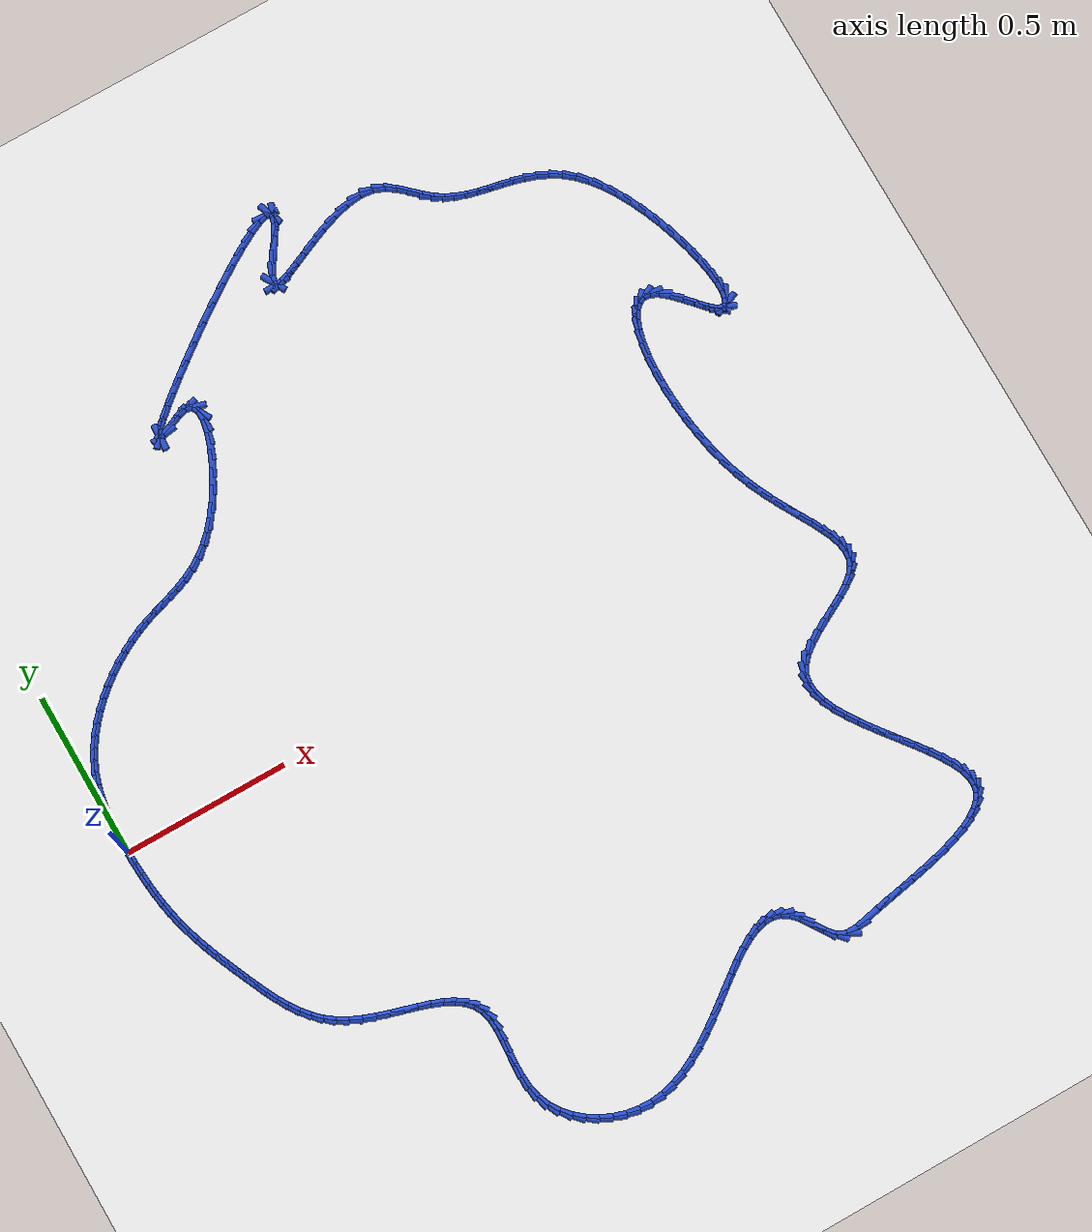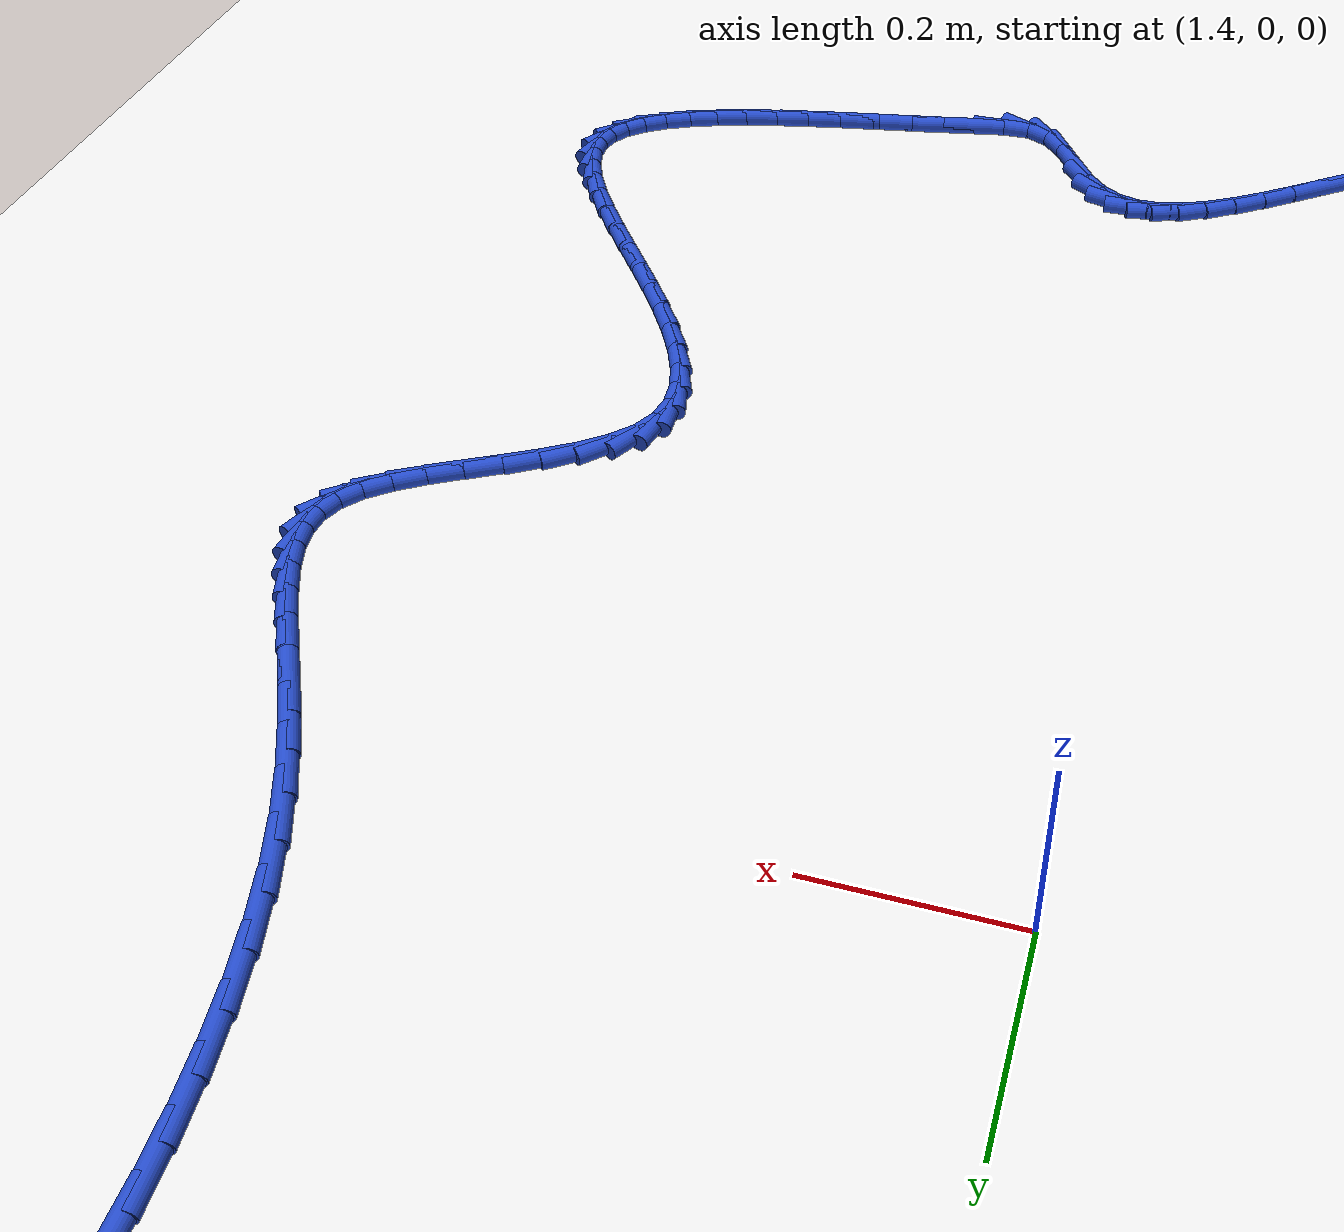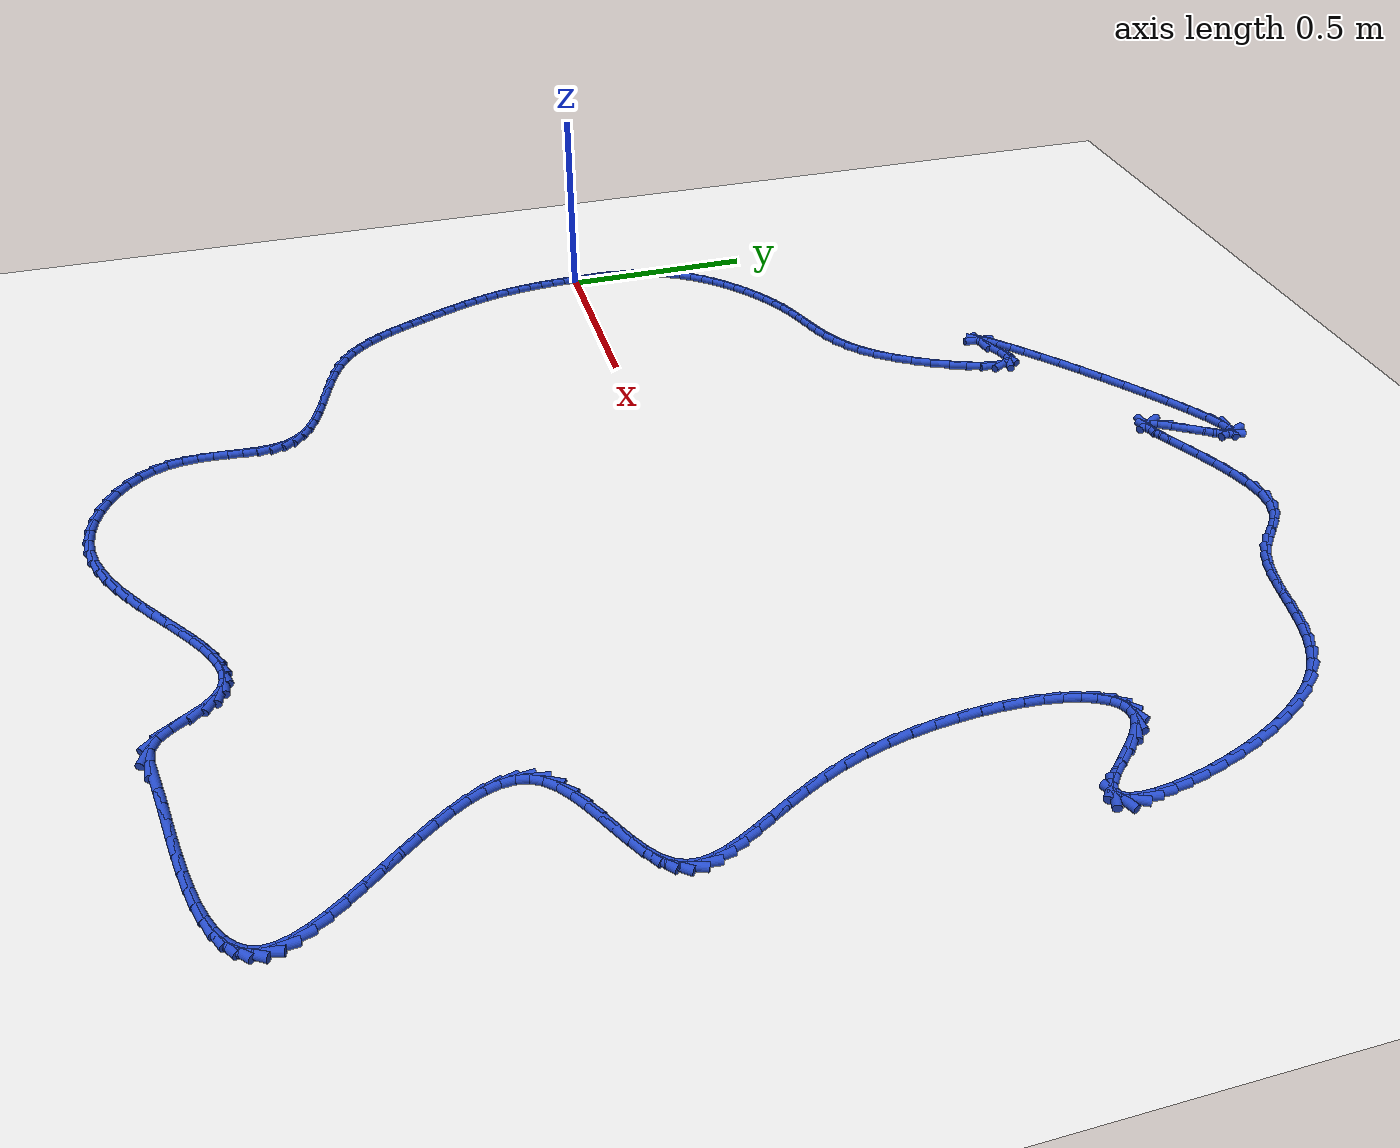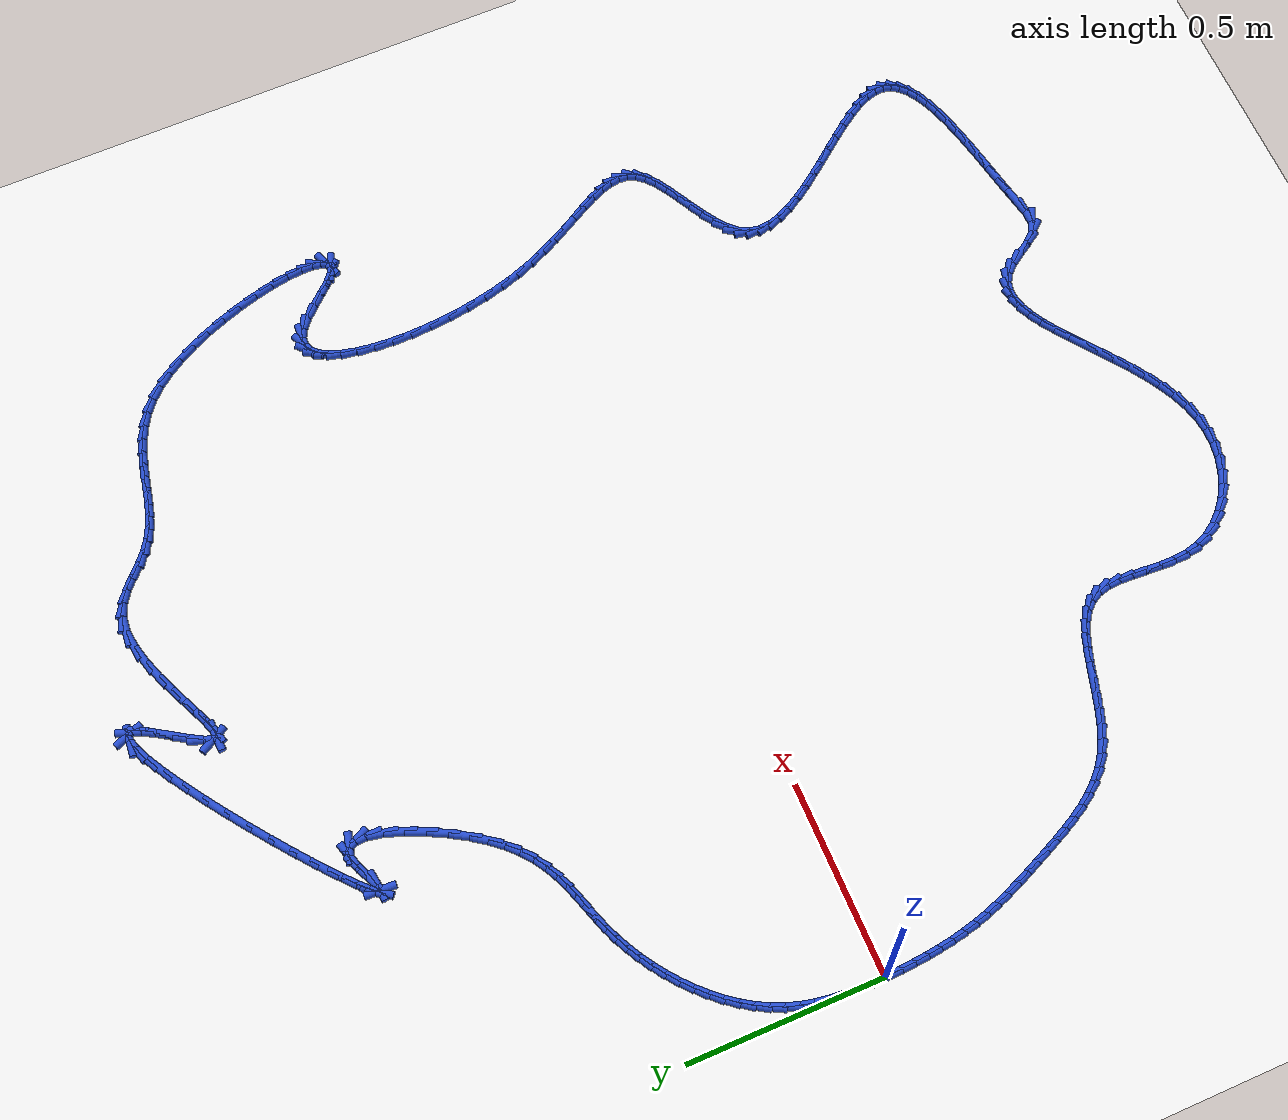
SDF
<sdf version="1.6">
 <world name="default">
  <light name="sun" type="directional">
   <pose>0 0 10 0 -0 0</pose>
   <diffuse>0.8 0.8 0.8 1</diffuse>
   <specular>0.2 0.2 0.2 1</specular>
   <attenuation>
    <range>1000</range>
    <constant>0.9</constant>
    <linear>0.01</linear>
    <quadratic>0.001</quadratic>
   </attenuation>
   <direction>-0.5 0.1 -0.9</direction>
  </light>
  <model name="ground_plane">
   <static>1</static>
   <link name="link">
    <collision name="collision">
     <geometry><plane><normal>0 0 1</normal><size>100 100</size></plane></geometry>
     <surface><friction><ode><mu>100</mu><mu2>50</mu2></ode></friction></surface>
    </collision>
    <visual name="visual">
     <cast_shadows>0</cast_shadows>
     <geometry><plane><normal>0 0 1</normal><size>100 100</size></plane></geometry>
     <material>
      <script><uri>file://media/materials/scripts/gazebo.material</uri><name>Gazebo/WhiteGlow</name></script>
     </material>
    </visual>
   </link>
  </model>
  <gravity>0 0 -9.8</gravity>
  <magnetic_field>6e-06 2.3e-05 -4.2e-05</magnetic_field>
  <atmosphere type="adiabatic"/>
  <physics name="default_physics" default="0" type="ode">
   <max_step_size>0.001</max_step_size>
   <real_time_factor>1</real_time_factor>
   <real_time_update_rate>1000</real_time_update_rate>
  </physics>
  <scene><ambient>0.4 0.4 0.4 1</ambient><background>0.7 0.7 0.7 1</background><shadows>1</shadows></scene>
  <spherical_coordinates>
   <surface_model>EARTH_WGS84</surface_model>
   <latitude_deg>0</latitude_deg>
   <longitude_deg>0</longitude_deg>
   <elevation>0</elevation>
   <heading_deg>0</heading_deg>
  </spherical_coordinates>
  <model name="line">
   <link name="link_0">
    <pose>-1.4203048459560108e-17 4.85722573273506e-17 0.01 0 1.57 -1.554861941099303</pose>
    <collision name="collision">
     <geometry><cylinder><radius>0.01</radius><length>0.08</length></cylinder></geometry>
    </collision>
    <visual name="visual">
     <material>
      <script><name>Gazebo/Blue</name><uri>file://media/materials/scripts/gazebo.material</uri></script>
     </material>
     <geometry><cylinder><radius>0.01</radius><length>0.08</length></cylinder></geometry>
    </visual>
   </link>
   <link name="link_1">
    <pose>-0.0005607315096017735 0.03518705157915492 0.01 0 1.57 1.5587283322600096</pose>
    <collision name="collision">
     <geometry><cylinder><radius>0.01</radius><length>0.08</length></cylinder></geometry>
    </collision>
    <visual name="visual">
     <material>
      <script><name>Gazebo/Blue</name><uri>file://media/materials/scripts/gazebo.material</uri></script>
     </material>
     <geometry><cylinder><radius>0.01</radius><length>0.08</length></cylinder></geometry>
    </visual>
   </link>
   <link name="link_2">
    <pose>-0.0001364163675874945 0.07034571377427733 0.01 0 1.57 1.5201912283098733</pose>
    <collision name="collision">
     <geometry><cylinder><radius>0.01</radius><length>0.08</length></cylinder></geometry>
    </collision>
    <visual name="visual">
     <material>
      <script><name>Gazebo/Blue</name><uri>file://media/materials/scripts/gazebo.material</uri></script>
     </material>
     <geometry><cylinder><radius>0.01</radius><length>0.08</length></cylinder></geometry>
    </visual>
   </link>
   <link name="link_3">
    <pose>0.0016350499765241493 0.10532151602201432 0.01 0 1.57 1.4706453482498205</pose>
    <collision name="collision">
     <geometry><cylinder><radius>0.01</radius><length>0.08</length></cylinder></geometry>
    </collision>
    <visual name="visual">
     <material>
      <script><name>Gazebo/Blue</name><uri>file://media/materials/scripts/gazebo.material</uri></script>
     </material>
     <geometry><cylinder><radius>0.01</radius><length>0.08</length></cylinder></geometry>
    </visual>
   </link>
   <link name="link_4">
    <pose>0.005115772073214488 0.13995998775901294 0.01 0 1.57 1.409611739790915</pose>
    <collision name="collision">
     <geometry><cylinder><radius>0.01</radius><length>0.08</length></cylinder></geometry>
    </collision>
    <visual name="visual">
     <material>
      <script><name>Gazebo/Blue</name><uri>file://media/materials/scripts/gazebo.material</uri></script>
     </material>
     <geometry><cylinder><radius>0.01</radius><length>0.08</length></cylinder></geometry>
    </visual>
   </link>
   <link name="link_5">
    <pose>0.010667854472964844 0.1741066584219202 0.01 0 1.57 1.3367915266916863</pose>
    <collision name="collision">
     <geometry><cylinder><radius>0.01</radius><length>0.08</length></cylinder></geometry>
    </collision>
    <visual name="visual">
     <material>
      <script><name>Gazebo/Blue</name><uri>file://media/materials/scripts/gazebo.material</uri></script>
     </material>
     <geometry><cylinder><radius>0.01</radius><length>0.08</length></cylinder></geometry>
    </visual>
   </link>
   <link name="link_6">
    <pose>0.018653401726256548 0.20760705744738317 0.01 0 1.57 1.2523183164123235</pose>
    <collision name="collision">
     <geometry><cylinder><radius>0.01</radius><length>0.08</length></cylinder></geometry>
    </collision>
    <visual name="visual">
     <material>
      <script><name>Gazebo/Blue</name><uri>file://media/materials/scripts/gazebo.material</uri></script>
     </material>
     <geometry><cylinder><radius>0.01</radius><length>0.08</length></cylinder></geometry>
    </visual>
   </link>
   <link name="link_7">
    <pose>0.029434515384613204 0.24030671456490235 0.01 0 1.57 1.1601722378784654</pose>
    <collision name="collision">
     <geometry><cylinder><radius>0.01</radius><length>0.08</length></cylinder></geometry>
    </collision>
    <visual name="visual">
     <material>
      <script><name>Gazebo/Blue</name><uri>file://media/materials/scripts/gazebo.material</uri></script>
     </material>
     <geometry><cylinder><radius>0.01</radius><length>0.08</length></cylinder></geometry>
    </visual>
   </link>
   <link name="link_8">
    <pose>0.04326001798189263 0.2720622213973947 0.01 0 1.57 1.0725680303783296</pose>
    <collision name="collision">
     <geometry><cylinder><radius>0.01</radius><length>0.08</length></cylinder></geometry>
    </collision>
    <visual name="visual">
     <material>
      <script><name>Gazebo/Blue</name><uri>file://media/materials/scripts/gazebo.material</uri></script>
     </material>
     <geometry><cylinder><radius>0.01</radius><length>0.08</length></cylinder></geometry>
    </visual>
   </link>
   <link name="link_9">
    <pose>0.05996546603199361 0.30277052571457014 0.01 0 1.57 0.9918570870051373</pose>
    <collision name="collision">
     <geometry><cylinder><radius>0.01</radius><length>0.08</length></cylinder></geometry>
    </collision>
    <visual name="visual">
     <material>
      <script><name>Gazebo/Blue</name><uri>file://media/materials/scripts/gazebo.material</uri></script>
     </material>
     <geometry><cylinder><radius>0.01</radius><length>0.08</length></cylinder></geometry>
    </visual>
   </link>
   <link name="link_10">
    <pose>0.07929219990354885 0.33233777565685635 0.01 0 1.57 0.917427633365914</pose>
    <collision name="collision">
     <geometry><cylinder><radius>0.01</radius><length>0.08</length></cylinder></geometry>
    </collision>
    <visual name="visual">
     <material>
      <script><name>Gazebo/Blue</name><uri>file://media/materials/scripts/gazebo.material</uri></script>
     </material>
     <geometry><cylinder><radius>0.01</radius><length>0.08</length></cylinder></geometry>
    </visual>
   </link>
   <link name="link_11">
    <pose>0.10098155996519091 0.3606701193646808 0.01 0 1.57 0.8485121434693215</pose>
    <collision name="collision">
     <geometry><cylinder><radius>0.01</radius><length>0.08</length></cylinder></geometry>
    </collision>
    <visual name="visual">
     <material>
      <script><name>Gazebo/Blue</name><uri>file://media/materials/scripts/gazebo.material</uri></script>
     </material>
     <geometry><cylinder><radius>0.01</radius><length>0.08</length></cylinder></geometry>
    </visual>
   </link>
   <link name="link_12">
    <pose>0.12477488658555244 0.38767370497847103 0.01 0 1.57 0.7842724643914043</pose>
    <collision name="collision">
     <geometry><cylinder><radius>0.01</radius><length>0.08</length></cylinder></geometry>
    </collision>
    <visual name="visual">
     <material>
      <script><name>Gazebo/Blue</name><uri>file://media/materials/scripts/gazebo.material</uri></script>
     </material>
     <geometry><cylinder><radius>0.01</radius><length>0.08</length></cylinder></geometry>
    </visual>
   </link>
   <link name="link_13">
    <pose>0.1504135201332661 0.4132546806386547 0.01 0 1.57 0.723850347277773</pose>
    <collision name="collision">
     <geometry><cylinder><radius>0.01</radius><length>0.08</length></cylinder></geometry>
    </collision>
    <visual name="visual">
     <material>
      <script><name>Gazebo/Blue</name><uri>file://media/materials/scripts/gazebo.material</uri></script>
     </material>
     <geometry><cylinder><radius>0.01</radius><length>0.08</length></cylinder></geometry>
    </visual>
   </link>
   <link name="link_14">
    <pose>0.17763880097696447 0.4373191944856595 0.01 0 1.57 0.6663911194407688</pose>
    <collision name="collision">
     <geometry><cylinder><radius>0.01</radius><length>0.08</length></cylinder></geometry>
    </collision>
    <visual name="visual">
     <material>
      <script><name>Gazebo/Blue</name><uri>file://media/materials/scripts/gazebo.material</uri></script>
     </material>
     <geometry><cylinder><radius>0.01</radius><length>0.08</length></cylinder></geometry>
    </visual>
   </link>
   <link name="link_15">
    <pose>0.20619206948528018 0.4597733946599125 0.01 0 1.57 0.6110479990104873</pose>
    <collision name="collision">
     <geometry><cylinder><radius>0.01</radius><length>0.08</length></cylinder></geometry>
    </collision>
    <visual name="visual">
     <material>
      <script><name>Gazebo/Blue</name><uri>file://media/materials/scripts/gazebo.material</uri></script>
     </material>
     <geometry><cylinder><radius>0.01</radius><length>0.08</length></cylinder></geometry>
    </visual>
   </link>
   <link name="link_16">
    <pose>0.23581466602684595 0.4805234293018418 0.01 0 1.57 0.5569726340803564</pose>
    <collision name="collision">
     <geometry><cylinder><radius>0.01</radius><length>0.08</length></cylinder></geometry>
    </collision>
    <visual name="visual">
     <material>
      <script><name>Gazebo/Blue</name><uri>file://media/materials/scripts/gazebo.material</uri></script>
     </material>
     <geometry><cylinder><radius>0.01</radius><length>0.08</length></cylinder></geometry>
    </visual>
   </link>
   <link name="link_17">
    <pose>0.26624793097029426 0.4994754465518747 0.01 0 1.57 0.5032952346625456</pose>
    <collision name="collision">
     <geometry><cylinder><radius>0.01</radius><length>0.08</length></cylinder></geometry>
    </collision>
    <visual name="visual">
     <material>
      <script><name>Gazebo/Blue</name><uri>file://media/materials/scripts/gazebo.material</uri></script>
     </material>
     <geometry><cylinder><radius>0.01</radius><length>0.08</length></cylinder></geometry>
    </visual>
   </link>
   <link name="link_18">
    <pose>0.2972332046842579 0.5165355945504388 0.01 0 1.57 0.44909569618928147</pose>
    <collision name="collision">
     <geometry><cylinder><radius>0.01</radius><length>0.08</length></cylinder></geometry>
    </collision>
    <visual name="visual">
     <material>
      <script><name>Gazebo/Blue</name><uri>file://media/materials/scripts/gazebo.material</uri></script>
     </material>
     <geometry><cylinder><radius>0.01</radius><length>0.08</length></cylinder></geometry>
    </visual>
   </link>
   <link name="link_19">
    <pose>0.3285118275373694 0.5316100214379618 0.01 0 1.57 0.39339054419586345</pose>
    <collision name="collision">
     <geometry><cylinder><radius>0.01</radius><length>0.08</length></cylinder></geometry>
    </collision>
    <visual name="visual">
     <material>
      <script><name>Gazebo/Blue</name><uri>file://media/materials/scripts/gazebo.material</uri></script>
     </material>
     <geometry><cylinder><radius>0.01</radius><length>0.08</length></cylinder></geometry>
    </visual>
   </link>
   <link name="link_20">
    <pose>0.3598253945690709 0.544605899940493 0.01 0 1.57 0.342266511397308</pose>
    <collision name="collision">
     <geometry><cylinder><radius>0.01</radius><length>0.08</length></cylinder></geometry>
    </collision>
    <visual name="visual">
     <material>
      <script><name>Gazebo/Blue</name><uri>file://media/materials/scripts/gazebo.material</uri></script>
     </material>
     <geometry><cylinder><radius>0.01</radius><length>0.08</length></cylinder></geometry>
    </visual>
   </link>
   <link name="link_21">
    <pose>0.39098437708469613 0.5557075041599884 0.01 0 1.57 0.3134970369056937</pose>
    <collision name="collision">
     <geometry><cylinder><radius>0.01</radius><length>0.08</length></cylinder></geometry>
    </collision>
    <visual name="visual">
     <material>
      <script><name>Gazebo/Blue</name><uri>file://media/materials/scripts/gazebo.material</uri></script>
     </material>
     <geometry><cylinder><radius>0.01</radius><length>0.08</length></cylinder></geometry>
    </visual>
   </link>
   <link name="link_22">
    <pose>0.42196096570349845 0.5657497335454369 0.01 0 1.57 0.3114217247632722</pose>
    <collision name="collision">
     <geometry><cylinder><radius>0.01</radius><length>0.08</length></cylinder></geometry>
    </collision>
    <visual name="visual">
     <material>
      <script><name>Gazebo/Blue</name><uri>file://media/materials/scripts/gazebo.material</uri></script>
     </material>
     <geometry><cylinder><radius>0.01</radius><length>0.08</length></cylinder></geometry>
    </visual>
   </link>
   <link name="link_23">
    <pose>0.45275053682494615 0.5756607680324459 0.01 0 1.57 0.33663825053759194</pose>
    <collision name="collision">
     <geometry><cylinder><radius>0.01</radius><length>0.08</length></cylinder></geometry>
    </collision>
    <visual name="visual">
     <material>
      <script><name>Gazebo/Blue</name><uri>file://media/materials/scripts/gazebo.material</uri></script>
     </material>
     <geometry><cylinder><radius>0.01</radius><length>0.08</length></cylinder></geometry>
    </visual>
   </link>
   <link name="link_24">
    <pose>0.4833484668485068 0.586368787556622 0.01 0 1.57 0.38820993739455334</pose>
    <collision name="collision">
     <geometry><cylinder><radius>0.01</radius><length>0.08</length></cylinder></geometry>
    </collision>
    <visual name="visual">
     <material>
      <script><name>Gazebo/Blue</name><uri>file://media/materials/scripts/gazebo.material</uri></script>
     </material>
     <geometry><cylinder><radius>0.01</radius><length>0.08</length></cylinder></geometry>
    </visual>
   </link>
   <link name="link_25">
    <pose>0.5137501321736483 0.5988019720535729 0.01 0 1.57 0.46328042237995387</pose>
    <collision name="collision">
     <geometry><cylinder><radius>0.01</radius><length>0.08</length></cylinder></geometry>
    </collision>
    <visual name="visual">
     <material>
      <script><name>Gazebo/Blue</name><uri>file://media/materials/scripts/gazebo.material</uri></script>
     </material>
     <geometry><cylinder><radius>0.01</radius><length>0.08</length></cylinder></geometry>
    </visual>
   </link>
   <link name="link_26">
    <pose>0.5439509091998385 0.6138885014589054 0.01 0 1.57 0.5567034667190686</pose>
    <collision name="collision">
     <geometry><cylinder><radius>0.01</radius><length>0.08</length></cylinder></geometry>
    </collision>
    <visual name="visual">
     <material>
      <script><name>Gazebo/Blue</name><uri>file://media/materials/scripts/gazebo.material</uri></script>
     </material>
     <geometry><cylinder><radius>0.01</radius><length>0.08</length></cylinder></geometry>
    </visual>
   </link>
   <link name="link_27">
    <pose>0.573946174326545 0.6325565557082264 0.01 0 1.57 0.6612846778918714</pose>
    <collision name="collision">
     <geometry><cylinder><radius>0.01</radius><length>0.08</length></cylinder></geometry>
    </collision>
    <visual name="visual">
     <material>
      <script><name>Gazebo/Blue</name><uri>file://media/materials/scripts/gazebo.material</uri></script>
     </material>
     <geometry><cylinder><radius>0.01</radius><length>0.08</length></cylinder></geometry>
    </visual>
   </link>
   <link name="link_28">
    <pose>0.6037313039532363 0.6557343147371439 0.01 0 1.57 0.768991452472936</pose>
    <collision name="collision">
     <geometry><cylinder><radius>0.01</radius><length>0.08</length></cylinder></geometry>
    </collision>
    <visual name="visual">
     <material>
      <script><name>Gazebo/Blue</name><uri>file://media/materials/scripts/gazebo.material</uri></script>
     </material>
     <geometry><cylinder><radius>0.01</radius><length>0.08</length></cylinder></geometry>
    </visual>
   </link>
   <link name="link_29">
    <pose>0.6333016744793794 0.6843499584812642 0.01 0 1.57 0.8724670537489958</pose>
    <collision name="collision">
     <geometry><cylinder><radius>0.01</radius><length>0.08</length></cylinder></geometry>
    </collision>
    <visual name="visual">
     <material>
      <script><name>Gazebo/Blue</name><uri>file://media/materials/scripts/gazebo.material</uri></script>
     </material>
     <geometry><cylinder><radius>0.01</radius><length>0.08</length></cylinder></geometry>
    </visual>
   </link>
   <link name="link_30">
    <pose>0.6626418207621968 0.7193021566672196 0.01 0 1.57 0.9601165431308157</pose>
    <collision name="collision">
     <geometry><cylinder><radius>0.01</radius><length>0.08</length></cylinder></geometry>
    </collision>
    <visual name="visual">
     <material>
      <script><name>Gazebo/Blue</name><uri>file://media/materials/scripts/gazebo.material</uri></script>
     </material>
     <geometry><cylinder><radius>0.01</radius><length>0.08</length></cylinder></geometry>
    </visual>
   </link>
   <link name="link_31">
    <pose>0.6912569975205123 0.7601849992191632 0.01 0 1.57 1.0309089559622644</pose>
    <collision name="collision">
     <geometry><cylinder><radius>0.01</radius><length>0.08</length></cylinder></geometry>
    </collision>
    <visual name="visual">
     <material>
      <script><name>Gazebo/Blue</name><uri>file://media/materials/scripts/gazebo.material</uri></script>
     </material>
     <geometry><cylinder><radius>0.01</radius><length>0.08</length></cylinder></geometry>
    </visual>
   </link>
   <link name="link_32">
    <pose>0.7179941788518448 0.8048007646880739 0.01 0 1.57 1.0959491649789292</pose>
    <collision name="collision">
     <geometry><cylinder><radius>0.01</radius><length>0.08</length></cylinder></geometry>
    </collision>
    <visual name="visual">
     <material>
      <script><name>Gazebo/Blue</name><uri>file://media/materials/scripts/gazebo.material</uri></script>
     </material>
     <geometry><cylinder><radius>0.01</radius><length>0.08</length></cylinder></geometry>
    </visual>
   </link>
   <link name="link_33">
    <pose>0.7416525631832369 0.8508216883167274 0.01 0 1.57 1.164950753278454</pose>
    <collision name="collision">
     <geometry><cylinder><radius>0.01</radius><length>0.08</length></cylinder></geometry>
    </collision>
    <visual name="visual">
     <material>
      <script><name>Gazebo/Blue</name><uri>file://media/materials/scripts/gazebo.material</uri></script>
     </material>
     <geometry><cylinder><radius>0.01</radius><length>0.08</length></cylinder></geometry>
    </visual>
   </link>
   <link name="link_34">
    <pose>0.7610313489417315 0.8959200053478993 0.01 0 1.57 1.2501414862681839</pose>
    <collision name="collision">
     <geometry><cylinder><radius>0.01</radius><length>0.08</length></cylinder></geometry>
    </collision>
    <visual name="visual">
     <material>
      <script><name>Gazebo/Blue</name><uri>file://media/materials/scripts/gazebo.material</uri></script>
     </material>
     <geometry><cylinder><radius>0.01</radius><length>0.08</length></cylinder></geometry>
    </visual>
   </link>
   <link name="link_35">
    <pose>0.7749297345543708 0.9377679510243652 0.01 0 1.57 1.3743759682598755</pose>
    <collision name="collision">
     <geometry><cylinder><radius>0.01</radius><length>0.08</length></cylinder></geometry>
    </collision>
    <visual name="visual">
     <material>
      <script><name>Gazebo/Blue</name><uri>file://media/materials/scripts/gazebo.material</uri></script>
     </material>
     <geometry><cylinder><radius>0.01</radius><length>0.08</length></cylinder></geometry>
    </visual>
   </link>
   <link name="link_36">
    <pose>0.7821469184481973 0.9740377605889001 0.01 0 1.57 -1.5473616973023543</pose>
    <collision name="collision">
     <geometry><cylinder><radius>0.01</radius><length>0.08</length></cylinder></geometry>
    </collision>
    <visual name="visual">
     <material>
      <script><name>Gazebo/Blue</name><uri>file://media/materials/scripts/gazebo.material</uri></script>
     </material>
     <geometry><cylinder><radius>0.01</radius><length>0.08</length></cylinder></geometry>
    </visual>
   </link>
   <link name="link_37">
    <pose>0.7814820990502537 1.0024016692842805 0.01 0 1.57 -1.0774886177360425</pose>
    <collision name="collision">
     <geometry><cylinder><radius>0.01</radius><length>0.08</length></cylinder></geometry>
    </collision>
    <visual name="visual">
     <material>
      <script><name>Gazebo/Blue</name><uri>file://media/materials/scripts/gazebo.material</uri></script>
     </material>
     <geometry><cylinder><radius>0.01</radius><length>0.08</length></cylinder></geometry>
    </visual>
   </link>
   <link name="link_38">
    <pose>0.7717344747875824 1.0205319123532814 0.01 0 1.57 -0.27115919203307887</pose>
    <collision name="collision">
     <geometry><cylinder><radius>0.01</radius><length>0.08</length></cylinder></geometry>
    </collision>
    <visual name="visual">
     <material>
      <script><name>Gazebo/Blue</name><uri>file://media/materials/scripts/gazebo.material</uri></script>
     </material>
     <geometry><cylinder><radius>0.01</radius><length>0.08</length></cylinder></geometry>
    </visual>
   </link>
   <link name="link_39">
    <pose>0.751703244087226 1.0261007250386787 0.01 0 1.57 0.2668726521005115</pose>
    <collision name="collision">
     <geometry><cylinder><radius>0.01</radius><length>0.08</length></cylinder></geometry>
    </collision>
    <visual name="visual">
     <material>
      <script><name>Gazebo/Blue</name><uri>file://media/materials/scripts/gazebo.material</uri></script>
     </material>
     <geometry><cylinder><radius>0.01</radius><length>0.08</length></cylinder></geometry>
    </visual>
   </link>
   <link name="link_40">
    <pose>0.7210690042762703 1.0177255031096377 0.01 0 1.57 0.42623050665465434</pose>
    <collision name="collision">
     <geometry><cylinder><radius>0.01</radius><length>0.08</length></cylinder></geometry>
    </collision>
    <visual name="visual">
     <material>
      <script><name>Gazebo/Blue</name><uri>file://media/materials/scripts/gazebo.material</uri></script>
     </material>
     <geometry><cylinder><radius>0.01</radius><length>0.08</length></cylinder></geometry>
    </visual>
   </link>
   <link name="link_41">
    <pose>0.6873282552412455 1.00240495819235 0.01 0 1.57 0.41125407069250974</pose>
    <collision name="collision">
     <geometry><cylinder><radius>0.01</radius><length>0.08</length></cylinder></geometry>
    </collision>
    <visual name="visual">
     <material>
      <script><name>Gazebo/Blue</name><uri>file://media/materials/scripts/gazebo.material</uri></script>
     </material>
     <geometry><cylinder><radius>0.01</radius><length>0.08</length></cylinder></geometry>
    </visual>
   </link>
   <link name="link_42">
    <pose>0.6618113247367805 0.9912764382031447 0.01 0 1.57 0.13711017147858523</pose>
    <collision name="collision">
     <geometry><cylinder><radius>0.01</radius><length>0.08</length></cylinder></geometry>
    </collision>
    <visual name="visual">
     <material>
      <script><name>Gazebo/Blue</name><uri>file://media/materials/scripts/gazebo.material</uri></script>
     </material>
     <geometry><cylinder><radius>0.01</radius><length>0.08</length></cylinder></geometry>
    </visual>
   </link>
   <link name="link_43">
    <pose>0.6497593873678029 0.9896135616719111 0.01 0 1.57 1.5209693389558194</pose>
    <collision name="collision">
     <geometry><cylinder><radius>0.01</radius><length>0.08</length></cylinder></geometry>
    </collision>
    <visual name="visual">
     <material>
      <script><name>Gazebo/Blue</name><uri>file://media/materials/scripts/gazebo.material</uri></script>
     </material>
     <geometry><cylinder><radius>0.01</radius><length>0.08</length></cylinder></geometry>
    </visual>
   </link>
   <link name="link_44">
    <pose>0.6501084986112181 0.9966142312797265 0.01 0 1.57 0.9074301202180165</pose>
    <collision name="collision">
     <geometry><cylinder><radius>0.01</radius><length>0.08</length></cylinder></geometry>
    </collision>
    <visual name="visual">
     <material>
      <script><name>Gazebo/Blue</name><uri>file://media/materials/scripts/gazebo.material</uri></script>
     </material>
     <geometry><cylinder><radius>0.01</radius><length>0.08</length></cylinder></geometry>
    </visual>
   </link>
   <link name="link_45">
    <pose>0.6615060448847625 1.011198183483963 0.01 0 1.57 0.7852465177851289</pose>
    <collision name="collision">
     <geometry><cylinder><radius>0.01</radius><length>0.08</length></cylinder></geometry>
    </collision>
    <visual name="visual">
     <material>
      <script><name>Gazebo/Blue</name><uri>file://media/materials/scripts/gazebo.material</uri></script>
     </material>
     <geometry><cylinder><radius>0.01</radius><length>0.08</length></cylinder></geometry>
    </visual>
   </link>
   <link name="link_46">
    <pose>0.6825994126061736 1.0322851547419927 0.01 0 1.57 0.7331304904036086</pose>
    <collision name="collision">
     <geometry><cylinder><radius>0.01</radius><length>0.08</length></cylinder></geometry>
    </collision>
    <visual name="visual">
     <material>
      <script><name>Gazebo/Blue</name><uri>file://media/materials/scripts/gazebo.material</uri></script>
     </material>
     <geometry><cylinder><radius>0.01</radius><length>0.08</length></cylinder></geometry>
    </visual>
   </link>
   <link name="link_47">
    <pose>0.712035988193188 1.0587948815111885 0.01 0 1.57 0.7027243470355717</pose>
    <collision name="collision">
     <geometry><cylinder><radius>0.01</radius><length>0.08</length></cylinder></geometry>
    </collision>
    <visual name="visual">
     <material>
      <script><name>Gazebo/Blue</name><uri>file://media/materials/scripts/gazebo.material</uri></script>
     </material>
     <geometry><cylinder><radius>0.01</radius><length>0.08</length></cylinder></geometry>
    </visual>
   </link>
   <link name="link_48">
    <pose>0.7484631580635427 1.0896471002489216 0.01 0 1.57 0.6814067698014981</pose>
    <collision name="collision">
     <geometry><cylinder><radius>0.01</radius><length>0.08</length></cylinder></geometry>
    </collision>
    <visual name="visual">
     <material>
      <script><name>Gazebo/Blue</name><uri>file://media/materials/scripts/gazebo.material</uri></script>
     </material>
     <geometry><cylinder><radius>0.01</radius><length>0.08</length></cylinder></geometry>
    </visual>
   </link>
   <link name="link_49">
    <pose>0.7905283086349744 1.123761547412565 0.01 0 1.57 0.6643417074533273</pose>
    <collision name="collision">
     <geometry><cylinder><radius>0.01</radius><length>0.08</length></cylinder></geometry>
    </collision>
    <visual name="visual">
     <material>
      <script><name>Gazebo/Blue</name><uri>file://media/materials/scripts/gazebo.material</uri></script>
     </material>
     <geometry><cylinder><radius>0.01</radius><length>0.08</length></cylinder></geometry>
    </visual>
   </link>
   <link name="link_50">
    <pose>0.8368788263252207 1.160057959459492 0.01 0 1.57 0.6491346908591793</pose>
    <collision name="collision">
     <geometry><cylinder><radius>0.01</radius><length>0.08</length></cylinder></geometry>
    </collision>
    <visual name="visual">
     <material>
      <script><name>Gazebo/Blue</name><uri>file://media/materials/scripts/gazebo.material</uri></script>
     </material>
     <geometry><cylinder><radius>0.01</radius><length>0.08</length></cylinder></geometry>
    </visual>
   </link>
   <link name="link_51">
    <pose>0.8861620975520185 1.1974560728470736 0.01 0 1.57 0.6342776916524369</pose>
    <collision name="collision">
     <geometry><cylinder><radius>0.01</radius><length>0.08</length></cylinder></geometry>
    </collision>
    <visual name="visual">
     <material>
      <script><name>Gazebo/Blue</name><uri>file://media/materials/scripts/gazebo.material</uri></script>
     </material>
     <geometry><cylinder><radius>0.01</radius><length>0.08</length></cylinder></geometry>
    </visual>
   </link>
   <link name="link_52">
    <pose>0.9370255087331034 1.2348756240326815 0.01 0 1.57 0.618526201779364</pose>
    <collision name="collision">
     <geometry><cylinder><radius>0.01</radius><length>0.08</length></cylinder></geometry>
    </collision>
    <visual name="visual">
     <material>
      <script><name>Gazebo/Blue</name><uri>file://media/materials/scripts/gazebo.material</uri></script>
     </material>
     <geometry><cylinder><radius>0.01</radius><length>0.08</length></cylinder></geometry>
    </visual>
   </link>
   <link name="link_53">
    <pose>0.9881164462862136 1.2712363494736898 0.01 0 1.57 0.6005200291970447</pose>
    <collision name="collision">
     <geometry><cylinder><radius>0.01</radius><length>0.08</length></cylinder></geometry>
    </collision>
    <visual name="visual">
     <material>
      <script><name>Gazebo/Blue</name><uri>file://media/materials/scripts/gazebo.material</uri></script>
     </material>
     <geometry><cylinder><radius>0.01</radius><length>0.08</length></cylinder></geometry>
    </visual>
   </link>
   <link name="link_54">
    <pose>1.0380822966290864 1.30545798562747 0.01 0 1.57 0.5783708839260531</pose>
    <collision name="collision">
     <geometry><cylinder><radius>0.01</radius><length>0.08</length></cylinder></geometry>
    </collision>
    <visual name="visual">
     <material>
      <script><name>Gazebo/Blue</name><uri>file://media/materials/scripts/gazebo.material</uri></script>
     </material>
     <geometry><cylinder><radius>0.01</radius><length>0.08</length></cylinder></geometry>
    </visual>
   </link>
   <link name="link_55">
    <pose>1.085570446179458 1.3364602689513942 0.01 0 1.57 0.5489308673238429</pose>
    <collision name="collision">
     <geometry><cylinder><radius>0.01</radius><length>0.08</length></cylinder></geometry>
    </collision>
    <visual name="visual">
     <material>
      <script><name>Gazebo/Blue</name><uri>file://media/materials/scripts/gazebo.material</uri></script>
     </material>
     <geometry><cylinder><radius>0.01</radius><length>0.08</length></cylinder></geometry>
    </visual>
   </link>
   <link name="link_56">
    <pose>1.1292282813550647 1.363162935902835 0.01 0 1.57 0.5060619291375661</pose>
    <collision name="collision">
     <geometry><cylinder><radius>0.01</radius><length>0.08</length></cylinder></geometry>
    </collision>
    <visual name="visual">
     <material>
      <script><name>Gazebo/Blue</name><uri>file://media/materials/scripts/gazebo.material</uri></script>
     </material>
     <geometry><cylinder><radius>0.01</radius><length>0.08</length></cylinder></geometry>
    </visual>
   </link>
   <link name="link_57">
    <pose>1.1677031885736444 1.3844857229391643 0.01 0 1.57 0.4355366535366532</pose>
    <collision name="collision">
     <geometry><cylinder><radius>0.01</radius><length>0.08</length></cylinder></geometry>
    </collision>
    <visual name="visual">
     <material>
      <script><name>Gazebo/Blue</name><uri>file://media/materials/scripts/gazebo.material</uri></script>
     </material>
     <geometry><cylinder><radius>0.01</radius><length>0.08</length></cylinder></geometry>
    </visual>
   </link>
   <link name="link_58">
    <pose>1.1996425542529345 1.3993483665177553 0.01 0 1.57 0.2955284686117981</pose>
    <collision name="collision">
     <geometry><cylinder><radius>0.01</radius><length>0.08</length></cylinder></geometry>
    </collision>
    <visual name="visual">
     <material>
      <script><name>Gazebo/Blue</name><uri>file://media/materials/scripts/gazebo.material</uri></script>
     </material>
     <geometry><cylinder><radius>0.01</radius><length>0.08</length></cylinder></geometry>
    </visual>
   </link>
   <link name="link_59">
    <pose>1.2236937648106707 1.4066706030959792 0.01 0 1.57 -0.08744658813504777</pose>
    <collision name="collision">
     <geometry><cylinder><radius>0.01</radius><length>0.08</length></cylinder></geometry>
    </collision>
    <visual name="visual">
     <material>
      <script><name>Gazebo/Blue</name><uri>file://media/materials/scripts/gazebo.material</uri></script>
     </material>
     <geometry><cylinder><radius>0.01</radius><length>0.08</length></cylinder></geometry>
    </visual>
   </link>
   <link name="link_60">
    <pose>1.2385042066645906 1.4053721691312089 0.01 0 1.57 -1.2046894658953824</pose>
    <collision name="collision">
     <geometry><cylinder><radius>0.01</radius><length>0.08</length></cylinder></geometry>
    </collision>
    <visual name="visual">
     <material>
      <script><name>Gazebo/Blue</name><uri>file://media/materials/scripts/gazebo.material</uri></script>
     </material>
     <geometry><cylinder><radius>0.01</radius><length>0.08</length></cylinder></geometry>
    </visual>
   </link>
   <link name="link_61">
    <pose>1.242721266232431 1.394372801080817 0.01 0 1.57 1.2348689751261193</pose>
    <collision name="collision">
     <geometry><cylinder><radius>0.01</radius><length>0.08</length></cylinder></geometry>
    </collision>
    <visual name="visual">
     <material>
      <script><name>Gazebo/Blue</name><uri>file://media/materials/scripts/gazebo.material</uri></script>
     </material>
     <geometry><cylinder><radius>0.01</radius><length>0.08</length></cylinder></geometry>
    </visual>
   </link>
   <link name="link_62">
    <pose>1.2351722170475903 1.3727522731677408 0.01 0 1.57 1.0527649954211737</pose>
    <collision name="collision">
     <geometry><cylinder><radius>0.01</radius><length>0.08</length></cylinder></geometry>
    </collision>
    <visual name="visual">
     <material>
      <script><name>Gazebo/Blue</name><uri>file://media/materials/scripts/gazebo.material</uri></script>
     </material>
     <geometry><cylinder><radius>0.01</radius><length>0.08</length></cylinder></geometry>
    </visual>
   </link>
   <link name="link_63">
    <pose>1.217904256672606 1.342454986383887 0.01 0 1.57 1.0005902580879384</pose>
    <collision name="collision">
     <geometry><cylinder><radius>0.01</radius><length>0.08</length></cylinder></geometry>
    </collision>
    <visual name="visual">
     <material>
      <script><name>Gazebo/Blue</name><uri>file://media/materials/scripts/gazebo.material</uri></script>
     </material>
     <geometry><cylinder><radius>0.01</radius><length>0.08</length></cylinder></geometry>
    </visual>
   </link>
   <link name="link_64">
    <pose>1.1957447245242527 1.3078987133613305 0.01 0 1.57 0.9979757512699563</pose>
    <collision name="collision">
     <geometry><cylinder><radius>0.01</radius><length>0.08</length></cylinder></geometry>
    </collision>
    <visual name="visual">
     <material>
      <script><name>Gazebo/Blue</name><uri>file://media/materials/scripts/gazebo.material</uri></script>
     </material>
     <geometry><cylinder><radius>0.01</radius><length>0.08</length></cylinder></geometry>
    </visual>
   </link>
   <link name="link_65">
    <pose>1.1736122956282742 1.2735824840624563 0.01 0 1.57 1.0444058567385293</pose>
    <collision name="collision">
     <geometry><cylinder><radius>0.01</radius><length>0.08</length></cylinder></geometry>
    </collision>
    <visual name="visual">
     <material>
      <script><name>Gazebo/Blue</name><uri>file://media/materials/scripts/gazebo.material</uri></script>
     </material>
     <geometry><cylinder><radius>0.01</radius><length>0.08</length></cylinder></geometry>
    </visual>
   </link>
   <link name="link_66">
    <pose>1.156425645010413 1.244005328449651 0.01 0 1.57 1.2244358652103724</pose>
    <collision name="collision">
     <geometry><cylinder><radius>0.01</radius><length>0.08</length></cylinder></geometry>
    </collision>
    <visual name="visual">
     <material>
      <script><name>Gazebo/Blue</name><uri>file://media/materials/scripts/gazebo.material</uri></script>
     </material>
     <geometry><cylinder><radius>0.01</radius><length>0.08</length></cylinder></geometry>
    </visual>
   </link>
   <link name="link_67">
    <pose>1.1490749589816625 1.2236382089960258 0.01 0 1.57 -1.0542798196957843</pose>
    <collision name="collision">
     <geometry><cylinder><radius>0.01</radius><length>0.08</length></cylinder></geometry>
    </collision>
    <visual name="visual">
     <material>
      <script><name>Gazebo/Blue</name><uri>file://media/materials/scripts/gazebo.material</uri></script>
     </material>
     <geometry><cylinder><radius>0.01</radius><length>0.08</length></cylinder></geometry>
    </visual>
   </link>
   <link name="link_68">
    <pose>1.1541560974288634 1.2146916849635583 0.01 0 1.57 0.04956153941908849</pose>
    <collision name="collision">
     <geometry><cylinder><radius>0.01</radius><length>0.08</length></cylinder></geometry>
    </collision>
    <visual name="visual">
     <material>
      <script><name>Gazebo/Blue</name><uri>file://media/materials/scripts/gazebo.material</uri></script>
     </material>
     <geometry><cylinder><radius>0.01</radius><length>0.08</length></cylinder></geometry>
    </visual>
   </link>
   <link name="link_69">
    <pose>1.1703239820658375 1.2154936469549638 0.01 0 1.57 0.32135105077253534</pose>
    <collision name="collision">
     <geometry><cylinder><radius>0.01</radius><length>0.08</length></cylinder></geometry>
    </collision>
    <visual name="visual">
     <material>
      <script><name>Gazebo/Blue</name><uri>file://media/materials/scripts/gazebo.material</uri></script>
     </material>
     <geometry><cylinder><radius>0.01</radius><length>0.08</length></cylinder></geometry>
    </visual>
   </link>
   <link name="link_70">
    <pose>1.1958451994721522 1.223989392243943 0.01 0 1.57 0.4031438198893011</pose>
    <collision name="collision">
     <geometry><cylinder><radius>0.01</radius><length>0.08</length></cylinder></geometry>
    </collision>
    <visual name="visual">
     <material>
      <script><name>Gazebo/Blue</name><uri>file://media/materials/scripts/gazebo.material</uri></script>
     </material>
     <geometry><cylinder><radius>0.01</radius><length>0.08</length></cylinder></geometry>
    </visual>
   </link>
   <link name="link_71">
    <pose>1.2289863362273763 1.2381242181041978 0.01 0 1.57 0.4261892374639192</pose>
    <collision name="collision">
     <geometry><cylinder><radius>0.01</radius><length>0.08</length></cylinder></geometry>
    </collision>
    <visual name="visual">
     <material>
      <script><name>Gazebo/Blue</name><uri>file://media/materials/scripts/gazebo.material</uri></script>
     </material>
     <geometry><cylinder><radius>0.01</radius><length>0.08</length></cylinder></geometry>
    </visual>
   </link>
   <link name="link_72">
    <pose>1.2680139789110771 1.2558434218094288 0.01 0 1.57 0.41933460419938257</pose>
    <collision name="collision">
     <geometry><cylinder><radius>0.01</radius><length>0.08</length></cylinder></geometry>
    </collision>
    <visual name="visual">
     <material>
      <script><name>Gazebo/Blue</name><uri>file://media/materials/scripts/gazebo.material</uri></script>
     </material>
     <geometry><cylinder><radius>0.01</radius><length>0.08</length></cylinder></geometry>
    </visual>
   </link>
   <link name="link_73">
    <pose>1.3111947141028244 1.2750923006333374 0.01 0 1.57 0.38961680345681954</pose>
    <collision name="collision">
     <geometry><cylinder><radius>0.01</radius><length>0.08</length></cylinder></geometry>
    </collision>
    <visual name="visual">
     <material>
      <script><name>Gazebo/Blue</name><uri>file://media/materials/scripts/gazebo.material</uri></script>
     </material>
     <geometry><cylinder><radius>0.01</radius><length>0.08</length></cylinder></geometry>
    </visual>
   </link>
   <link name="link_74">
    <pose>1.3567951283821853 1.2938161518496252 0.01 0 1.57 0.33559241292047726</pose>
    <collision name="collision">
     <geometry><cylinder><radius>0.01</radius><length>0.08</length></cylinder></geometry>
    </collision>
    <visual name="visual">
     <material>
      <script><name>Gazebo/Blue</name><uri>file://media/materials/scripts/gazebo.material</uri></script>
     </material>
     <geometry><cylinder><radius>0.01</radius><length>0.08</length></cylinder></geometry>
    </visual>
   </link>
   <link name="link_75">
    <pose>1.4030818083287293 1.3099602727319932 0.01 0 1.57 0.2491311210069129</pose>
    <collision name="collision">
     <geometry><cylinder><radius>0.01</radius><length>0.08</length></cylinder></geometry>
    </collision>
    <visual name="visual">
     <material>
      <script><name>Gazebo/Blue</name><uri>file://media/materials/scripts/gazebo.material</uri></script>
     </material>
     <geometry><cylinder><radius>0.01</radius><length>0.08</length></cylinder></geometry>
    </visual>
   </link>
   <link name="link_76">
    <pose>1.448321340522023 1.3214699605541422 0.01 0 1.57 0.11305027568607978</pose>
    <collision name="collision">
     <geometry><cylinder><radius>0.01</radius><length>0.08</length></cylinder></geometry>
    </collision>
    <visual name="visual">
     <material>
      <script><name>Gazebo/Blue</name><uri>file://media/materials/scripts/gazebo.material</uri></script>
     </material>
     <geometry><cylinder><radius>0.01</radius><length>0.08</length></cylinder></geometry>
    </visual>
   </link>
   <link name="link_77">
    <pose>1.4907803115416356 1.3262905125897737 0.01 0 1.57 -0.10230702233685758</pose>
    <collision name="collision">
     <geometry><cylinder><radius>0.01</radius><length>0.08</length></cylinder></geometry>
    </collision>
    <visual name="visual">
     <material>
      <script><name>Gazebo/Blue</name><uri>file://media/materials/scripts/gazebo.material</uri></script>
     </material>
     <geometry><cylinder><radius>0.01</radius><length>0.08</length></cylinder></geometry>
    </visual>
   </link>
   <link name="link_78">
    <pose>1.5287422347250164 1.3223931341706687 0.01 0 1.57 -0.374079910380433</pose>
    <collision name="collision">
     <geometry><cylinder><radius>0.01</radius><length>0.08</length></cylinder></geometry>
    </collision>
    <visual name="visual">
     <material>
      <script><name>Gazebo/Blue</name><uri>file://media/materials/scripts/gazebo.material</uri></script>
     </material>
     <geometry><cylinder><radius>0.01</radius><length>0.08</length></cylinder></geometry>
    </visual>
   </link>
   <link name="link_79">
    <pose>1.561624599189698 1.309484691443154 0.01 0 1.57 -0.5891040869339764</pose>
    <collision name="collision">
     <geometry><cylinder><radius>0.01</radius><length>0.08</length></cylinder></geometry>
    </collision>
    <visual name="visual">
     <material>
      <script><name>Gazebo/Blue</name><uri>file://media/materials/scripts/gazebo.material</uri></script>
     </material>
     <geometry><cylinder><radius>0.01</radius><length>0.08</length></cylinder></geometry>
    </visual>
   </link>
   <link name="link_80">
    <pose>1.5906742254262527 1.290072021096816 0.01 0 1.57 -0.7157350560996167</pose>
    <collision name="collision">
     <geometry><cylinder><radius>0.01</radius><length>0.08</length></cylinder></geometry>
    </collision>
    <visual name="visual">
     <material>
      <script><name>Gazebo/Blue</name><uri>file://media/materials/scripts/gazebo.material</uri></script>
     </material>
     <geometry><cylinder><radius>0.01</radius><length>0.08</length></cylinder></geometry>
    </visual>
   </link>
   <link name="link_81">
    <pose>1.6173039809465752 1.2669161110238878 0.01 0 1.57 -0.7555725424011854</pose>
    <collision name="collision">
     <geometry><cylinder><radius>0.01</radius><length>0.08</length></cylinder></geometry>
    </collision>
    <visual name="visual">
     <material>
      <script><name>Gazebo/Blue</name><uri>file://media/materials/scripts/gazebo.material</uri></script>
     </material>
     <geometry><cylinder><radius>0.01</radius><length>0.08</length></cylinder></geometry>
    </visual>
   </link>
   <link name="link_82">
    <pose>1.6429267332625608 1.2427779491166044 0.01 0 1.57 -0.7097145401557308</pose>
    <collision name="collision">
     <geometry><cylinder><radius>0.01</radius><length>0.08</length></cylinder></geometry>
    </collision>
    <visual name="visual">
     <material>
      <script><name>Gazebo/Blue</name><uri>file://media/materials/scripts/gazebo.material</uri></script>
     </material>
     <geometry><cylinder><radius>0.01</radius><length>0.08</length></cylinder></geometry>
    </visual>
   </link>
   <link name="link_83">
    <pose>1.6689553498861043 1.2204185232671982 0.01 0 1.57 -0.5828367995028781</pose>
    <collision name="collision">
     <geometry><cylinder><radius>0.01</radius><length>0.08</length></cylinder></geometry>
    </collision>
    <visual name="visual">
     <material>
      <script><name>Gazebo/Blue</name><uri>file://media/materials/scripts/gazebo.material</uri></script>
     </material>
     <geometry><cylinder><radius>0.01</radius><length>0.08</length></cylinder></geometry>
    </visual>
   </link>
   <link name="link_84">
    <pose>1.6966120816576111 1.2021863623528262 0.01 0 1.57 -0.4488596513356843</pose>
    <collision name="collision">
     <geometry><cylinder><radius>0.01</radius><length>0.08</length></cylinder></geometry>
    </collision>
    <visual name="visual">
     <material>
      <script><name>Gazebo/Blue</name><uri>file://media/materials/scripts/gazebo.material</uri></script>
     </material>
     <geometry><cylinder><radius>0.01</radius><length>0.08</length></cylinder></geometry>
    </visual>
   </link>
   <link name="link_85">
    <pose>1.7260088415278938 1.188027430623055 0.01 0 1.57 -0.34274368351698703</pose>
    <collision name="collision">
     <geometry><cylinder><radius>0.01</radius><length>0.08</length></cylinder></geometry>
    </collision>
    <visual name="visual">
     <material>
      <script><name>Gazebo/Blue</name><uri>file://media/materials/scripts/gazebo.material</uri></script>
     </material>
     <geometry><cylinder><radius>0.01</radius><length>0.08</length></cylinder></geometry>
    </visual>
   </link>
   <link name="link_86">
    <pose>1.7568565974621981 1.1770201219698524 0.01 0 1.57 -0.26766737884194924</pose>
    <collision name="collision">
     <geometry><cylinder><radius>0.01</radius><length>0.08</length></cylinder></geometry>
    </collision>
    <visual name="visual">
     <material>
      <script><name>Gazebo/Blue</name><uri>file://media/materials/scripts/gazebo.material</uri></script>
     </material>
     <geometry><cylinder><radius>0.01</radius><length>0.08</length></cylinder></geometry>
    </visual>
   </link>
   <link name="link_87">
    <pose>1.7888657740358302 1.1682416544904506 0.01 0 1.57 -0.2234606583939659</pose>
    <collision name="collision">
     <geometry><cylinder><radius>0.01</radius><length>0.08</length></cylinder></geometry>
    </collision>
    <visual name="visual">
     <material>
      <script><name>Gazebo/Blue</name><uri>file://media/materials/scripts/gazebo.material</uri></script>
     </material>
     <geometry><cylinder><radius>0.01</radius><length>0.08</length></cylinder></geometry>
    </visual>
   </link>
   <link name="link_88">
    <pose>1.8217467958240954 1.1607692462820798 0.01 0 1.57 -0.20876146430850315</pose>
    <collision name="collision">
     <geometry><cylinder><radius>0.01</radius><length>0.08</length></cylinder></geometry>
    </collision>
    <visual name="visual">
     <material>
      <script><name>Gazebo/Blue</name><uri>file://media/materials/scripts/gazebo.material</uri></script>
     </material>
     <geometry><cylinder><radius>0.01</radius><length>0.08</length></cylinder></geometry>
    </visual>
   </link>
   <link name="link_89">
    <pose>1.8552100874023005 1.1536801154419711 0.01 0 1.57 -0.22225992390580582</pose>
    <collision name="collision">
     <geometry><cylinder><radius>0.01</radius><length>0.08</length></cylinder></geometry>
    </collision>
    <visual name="visual">
     <material>
      <script><name>Gazebo/Blue</name><uri>file://media/materials/scripts/gazebo.material</uri></script>
     </material>
     <geometry><cylinder><radius>0.01</radius><length>0.08</length></cylinder></geometry>
    </visual>
   </link>
   <link name="link_90">
    <pose>1.8889660733457516 1.1460514800673554 0.01 0 1.57 -0.26304809300690674</pose>
    <collision name="collision">
     <geometry><cylinder><radius>0.01</radius><length>0.08</length></cylinder></geometry>
    </collision>
    <visual name="visual">
     <material>
      <script><name>Gazebo/Blue</name><uri>file://media/materials/scripts/gazebo.material</uri></script>
     </material>
     <geometry><cylinder><radius>0.01</radius><length>0.08</length></cylinder></geometry>
    </visual>
   </link>
   <link name="link_91">
    <pose>1.9227251782297547 1.1369605582554636 0.01 0 1.57 -0.33028809346728794</pose>
    <collision name="collision">
     <geometry><cylinder><radius>0.01</radius><length>0.08</length></cylinder></geometry>
    </collision>
    <visual name="visual">
     <material>
      <script><name>Gazebo/Blue</name><uri>file://media/materials/scripts/gazebo.material</uri></script>
     </material>
     <geometry><cylinder><radius>0.01</radius><length>0.08</length></cylinder></geometry>
    </visual>
   </link>
   <link name="link_92">
    <pose>1.9561978266296154 1.1254845681035266 0.01 0 1.57 -0.42235740653796067</pose>
    <collision name="collision">
     <geometry><cylinder><radius>0.01</radius><length>0.08</length></cylinder></geometry>
    </collision>
    <visual name="visual">
     <material>
      <script><name>Gazebo/Blue</name><uri>file://media/materials/scripts/gazebo.material</uri></script>
     </material>
     <geometry><cylinder><radius>0.01</radius><length>0.08</length></cylinder></geometry>
    </visual>
   </link>
   <link name="link_93">
    <pose>1.9890944431206403 1.1107007277087757 0.01 0 1.57 -0.5357203083800188</pose>
    <collision name="collision">
     <geometry><cylinder><radius>0.01</radius><length>0.08</length></cylinder></geometry>
    </collision>
    <visual name="visual">
     <material>
      <script><name>Gazebo/Blue</name><uri>file://media/materials/scripts/gazebo.material</uri></script>
     </material>
     <geometry><cylinder><radius>0.01</radius><length>0.08</length></cylinder></geometry>
    </visual>
   </link>
   <link name="link_94">
    <pose>2.021125452278136 1.0916862551684412 0.01 0 1.57 -0.6641304443680188</pose>
    <collision name="collision">
     <geometry><cylinder><radius>0.01</radius><length>0.08</length></cylinder></geometry>
    </collision>
    <visual name="visual">
     <material>
      <script><name>Gazebo/Blue</name><uri>file://media/materials/scripts/gazebo.material</uri></script>
     </material>
     <geometry><cylinder><radius>0.01</radius><length>0.08</length></cylinder></geometry>
    </visual>
   </link>
   <link name="link_95">
    <pose>2.052001278677407 1.0675183685797547 0.01 0 1.57 -0.7986546403188867</pose>
    <collision name="collision">
     <geometry><cylinder><radius>0.01</radius><length>0.08</length></cylinder></geometry>
    </collision>
    <visual name="visual">
     <material>
      <script><name>Gazebo/Blue</name><uri>file://media/materials/scripts/gazebo.material</uri></script>
     </material>
     <geometry><cylinder><radius>0.01</radius><length>0.08</length></cylinder></geometry>
    </visual>
   </link>
   <link name="link_96">
    <pose>2.0814332812814436 1.037295506308682 0.01 0 1.57 -0.9183482344592655</pose>
    <collision name="collision">
     <geometry><cylinder><radius>0.01</radius><length>0.08</length></cylinder></geometry>
    </collision>
    <visual name="visual">
     <material>
      <script><name>Gazebo/Blue</name><uri>file://media/materials/scripts/gazebo.material</uri></script>
     </material>
     <geometry><cylinder><radius>0.01</radius><length>0.08</length></cylinder></geometry>
    </visual>
   </link>
   <link name="link_97">
    <pose>2.1091714130668673 1.0009925901723473 0.01 0 1.57 -1.0109510828171921</pose>
    <collision name="collision">
     <geometry><cylinder><radius>0.01</radius><length>0.08</length></cylinder></geometry>
    </collision>
    <visual name="visual">
     <material>
      <script><name>Gazebo/Blue</name><uri>file://media/materials/scripts/gazebo.material</uri></script>
     </material>
     <geometry><cylinder><radius>0.01</radius><length>0.08</length></cylinder></geometry>
    </visual>
   </link>
   <link name="link_98">
    <pose>2.1350171160579285 0.9597538761387163 0.01 0 1.57 -1.0845611030074251</pose>
    <collision name="collision">
     <geometry><cylinder><radius>0.01</radius><length>0.08</length></cylinder></geometry>
    </collision>
    <visual name="visual">
     <material>
      <script><name>Gazebo/Blue</name><uri>file://media/materials/scripts/gazebo.material</uri></script>
     </material>
     <geometry><cylinder><radius>0.01</radius><length>0.08</length></cylinder></geometry>
    </visual>
   </link>
   <link name="link_99">
    <pose>2.1587754130440895 0.9148049405971295 0.01 0 1.57 -1.1456515527131634</pose>
    <collision name="collision">
     <geometry><cylinder><radius>0.01</radius><length>0.08</length></cylinder></geometry>
    </collision>
    <visual name="visual">
     <material>
      <script><name>Gazebo/Blue</name><uri>file://media/materials/scripts/gazebo.material</uri></script>
     </material>
     <geometry><cylinder><radius>0.01</radius><length>0.08</length></cylinder></geometry>
    </visual>
   </link>
   <link name="link_100">
    <pose>2.18025132681481 0.867371359936929 0.01 0 1.57 -1.1987901679226376</pose>
    <collision name="collision">
     <geometry><cylinder><radius>0.01</radius><length>0.08</length></cylinder></geometry>
    </collision>
    <visual name="visual">
     <material>
      <script><name>Gazebo/Blue</name><uri>file://media/materials/scripts/gazebo.material</uri></script>
     </material>
     <geometry><cylinder><radius>0.01</radius><length>0.08</length></cylinder></geometry>
    </visual>
   </link>
   <link name="link_101">
    <pose>2.1992498801595524 0.8186787105474562 0.01 0 1.57 -1.2474919386697605</pose>
    <collision name="collision">
     <geometry><cylinder><radius>0.01</radius><length>0.08</length></cylinder></geometry>
    </collision>
    <visual name="visual">
     <material>
      <script><name>Gazebo/Blue</name><uri>file://media/materials/scripts/gazebo.material</uri></script>
     </material>
     <geometry><cylinder><radius>0.01</radius><length>0.08</length></cylinder></geometry>
    </visual>
   </link>
   <link name="link_102">
    <pose>2.21557609586778 0.7699525688180515 0.01 0 1.57 -1.294876183848476</pose>
    <collision name="collision">
     <geometry><cylinder><radius>0.01</radius><length>0.08</length></cylinder></geometry>
    </collision>
    <visual name="visual">
     <material>
      <script><name>Gazebo/Blue</name><uri>file://media/materials/scripts/gazebo.material</uri></script>
     </material>
     <geometry><cylinder><radius>0.01</radius><length>0.08</length></cylinder></geometry>
    </visual>
   </link>
   <link name="link_103">
    <pose>2.2290349967289527 0.7224185111380577 0.01 0 1.57 -1.3443103755115244</pose>
    <collision name="collision">
     <geometry><cylinder><radius>0.01</radius><length>0.08</length></cylinder></geometry>
    </collision>
    <visual name="visual">
     <material>
      <script><name>Gazebo/Blue</name><uri>file://media/materials/scripts/gazebo.material</uri></script>
     </material>
     <geometry><cylinder><radius>0.01</radius><length>0.08</length></cylinder></geometry>
    </visual>
   </link>
   <link name="link_104">
    <pose>2.2394316055325327 0.6773021138968153 0.01 0 1.57 -1.4003235109231205</pose>
    <collision name="collision">
     <geometry><cylinder><radius>0.01</radius><length>0.08</length></cylinder></geometry>
    </collision>
    <visual name="visual">
     <material>
      <script><name>Gazebo/Blue</name><uri>file://media/materials/scripts/gazebo.material</uri></script>
     </material>
     <geometry><cylinder><radius>0.01</radius><length>0.08</length></cylinder></geometry>
    </visual>
   </link>
   <link name="link_105">
    <pose>2.2465709450679823 0.6358289534836659 0.01 0 1.57 -1.4704066537792737</pose>
    <collision name="collision">
     <geometry><cylinder><radius>0.01</radius><length>0.08</length></cylinder></geometry>
    </collision>
    <visual name="visual">
     <material>
      <script><name>Gazebo/Blue</name><uri>file://media/materials/scripts/gazebo.material</uri></script>
     </material>
     <geometry><cylinder><radius>0.01</radius><length>0.08</length></cylinder></geometry>
    </visual>
   </link>
   <link name="link_106">
    <pose>2.250258038124763 0.5992246062879505 0.01 0 1.57 -1.5694895617899398</pose>
    <collision name="collision">
     <geometry><cylinder><radius>0.01</radius><length>0.08</length></cylinder></geometry>
    </collision>
    <visual name="visual">
     <material>
      <script><name>Gazebo/Blue</name><uri>file://media/materials/scripts/gazebo.material</uri></script>
     </material>
     <geometry><cylinder><radius>0.01</radius><length>0.08</length></cylinder></geometry>
    </visual>
   </link>
   <link name="link_107">
    <pose>2.250297907492337 0.5687146486990106 0.01 0 1.57 1.4082780924493747</pose>
    <collision name="collision">
     <geometry><cylinder><radius>0.01</radius><length>0.08</length></cylinder></geometry>
    </collision>
    <visual name="visual">
     <material>
      <script><name>Gazebo/Blue</name><uri>file://media/materials/scripts/gazebo.material</uri></script>
     </material>
     <geometry><cylinder><radius>0.01</radius><length>0.08</length></cylinder></geometry>
    </visual>
   </link>
   <link name="link_108">
    <pose>2.246495575960165 0.545524657106188 0.01 0 1.57 1.0792912766523763</pose>
    <collision name="collision">
     <geometry><cylinder><radius>0.01</radius><length>0.08</length></cylinder></geometry>
    </collision>
    <visual name="visual">
     <material>
      <script><name>Gazebo/Blue</name><uri>file://media/materials/scripts/gazebo.material</uri></script>
     </material>
     <geometry><cylinder><radius>0.01</radius><length>0.08</length></cylinder></geometry>
    </visual>
   </link>
   <link name="link_109">
    <pose>2.238656066317709 0.5308802078988237 0.01 0 1.57 0.3836919063397347</pose>
    <collision name="collision">
     <geometry><cylinder><radius>0.01</radius><length>0.08</length></cylinder></geometry>
    </collision>
    <visual name="visual">
     <material>
      <script><name>Gazebo/Blue</name><uri>file://media/materials/scripts/gazebo.material</uri></script>
     </material>
     <geometry><cylinder><radius>0.01</radius><length>0.08</length></cylinder></geometry>
    </visual>
   </link>
   <link name="link_110">
    <pose>2.226584401354431 0.526006877466259 0.01 0 1.57 -0.3553823284577421</pose>
    <collision name="collision">
     <geometry><cylinder><radius>0.01</radius><length>0.08</length></cylinder></geometry>
    </collision>
    <visual name="visual">
     <material>
      <script><name>Gazebo/Blue</name><uri>file://media/materials/scripts/gazebo.material</uri></script>
     </material>
     <geometry><cylinder><radius>0.01</radius><length>0.08</length></cylinder></geometry>
    </visual>
   </link>
   <link name="link_111">
    <pose>2.2100856038597927 0.5321302421978354 0.01 0 1.57 -0.6986953365020279</pose>
    <collision name="collision">
     <geometry><cylinder><radius>0.01</radius><length>0.08</length></cylinder></geometry>
    </collision>
    <visual name="visual">
     <material>
      <script><name>Gazebo/Blue</name><uri>file://media/materials/scripts/gazebo.material</uri></script>
     </material>
     <geometry><cylinder><radius>0.01</radius><length>0.08</length></cylinder></geometry>
    </visual>
   </link>
   <link name="link_112">
    <pose>2.189180605358662 0.549691707169173 0.01 0 1.57 -0.8113289779576883</pose>
    <collision name="collision">
     <geometry><cylinder><radius>0.01</radius><length>0.08</length></cylinder></geometry>
    </collision>
    <visual name="visual">
     <material>
      <script><name>Gazebo/Blue</name><uri>file://media/materials/scripts/gazebo.material</uri></script>
     </material>
     <geometry><cylinder><radius>0.01</radius><length>0.08</length></cylinder></geometry>
    </visual>
   </link>
   <link name="link_113">
    <pose>2.164977659938133 0.5751835683082018 0.01 0 1.57 -0.8332926058131561</pose>
    <collision name="collision">
     <geometry><cylinder><radius>0.01</radius><length>0.08</length></cylinder></geometry>
    </collision>
    <visual name="visual">
     <material>
      <script><name>Gazebo/Blue</name><uri>file://media/materials/scripts/gazebo.material</uri></script>
     </material>
     <geometry><cylinder><radius>0.01</radius><length>0.08</length></cylinder></geometry>
    </visual>
   </link>
   <link name="link_114">
    <pose>2.1389265441461855 0.6038577265383765 0.01 0 1.57 -0.7976932239954626</pose>
    <collision name="collision">
     <geometry><cylinder><radius>0.01</radius><length>0.08</length></cylinder></geometry>
    </collision>
    <visual name="visual">
     <material>
      <script><name>Gazebo/Blue</name><uri>file://media/materials/scripts/gazebo.material</uri></script>
     </material>
     <geometry><cylinder><radius>0.01</radius><length>0.08</length></cylinder></geometry>
    </visual>
   </link>
   <link name="link_115">
    <pose>2.112477157342166 0.630965636737518 0.01 0 1.57 -0.6860470212012354</pose>
    <collision name="collision">
     <geometry><cylinder><radius>0.01</radius><length>0.08</length></cylinder></geometry>
    </collision>
    <visual name="visual">
     <material>
      <script><name>Gazebo/Blue</name><uri>file://media/materials/scripts/gazebo.material</uri></script>
     </material>
     <geometry><cylinder><radius>0.01</radius><length>0.08</length></cylinder></geometry>
    </visual>
   </link>
   <link name="link_116">
    <pose>2.0870792900496493 0.6517591758311445 0.01 0 1.57 -0.4388906714517904</pose>
    <collision name="collision">
     <geometry><cylinder><radius>0.01</radius><length>0.08</length></cylinder></geometry>
    </collision>
    <visual name="visual">
     <material>
      <script><name>Gazebo/Blue</name><uri>file://media/materials/scripts/gazebo.material</uri></script>
     </material>
     <geometry><cylinder><radius>0.01</radius><length>0.08</length></cylinder></geometry>
    </visual>
   </link>
   <link name="link_117">
    <pose>2.063884296233639 0.6626475099328232 0.01 0 1.57 -0.05154768172381478</pose>
    <collision name="collision">
     <geometry><cylinder><radius>0.01</radius><length>0.08</length></cylinder></geometry>
    </collision>
    <visual name="visual">
     <material>
      <script><name>Gazebo/Blue</name><uri>file://media/materials/scripts/gazebo.material</uri></script>
     </material>
     <geometry><cylinder><radius>0.01</radius><length>0.08</length></cylinder></geometry>
    </visual>
   </link>
   <link name="link_118">
    <pose>2.0430944647306144 0.6637201277588787 0.01 0 1.57 0.40721393788235904</pose>
    <collision name="collision">
     <geometry><cylinder><radius>0.01</radius><length>0.08</length></cylinder></geometry>
    </collision>
    <visual name="visual">
     <material>
      <script><name>Gazebo/Blue</name><uri>file://media/materials/scripts/gazebo.material</uri></script>
     </material>
     <geometry><cylinder><radius>0.01</radius><length>0.08</length></cylinder></geometry>
    </visual>
   </link>
   <link name="link_119">
    <pose>2.0247238497161435 0.6557964619002551 0.01 0 1.57 0.7904912371703323</pose>
    <collision name="collision">
     <geometry><cylinder><radius>0.01</radius><length>0.08</length></cylinder></geometry>
    </collision>
    <visual name="visual">
     <material>
      <script><name>Gazebo/Blue</name><uri>file://media/materials/scripts/gazebo.material</uri></script>
     </material>
     <geometry><cylinder><radius>0.01</radius><length>0.08</length></cylinder></geometry>
    </visual>
   </link>
   <link name="link_120">
    <pose>2.0087865053657943 0.6396959449478968 0.01 0 1.57 1.0489073732488041</pose>
    <collision name="collision">
     <geometry><cylinder><radius>0.01</radius><length>0.08</length></cylinder></geometry>
    </collision>
    <visual name="visual">
     <material>
      <script><name>Gazebo/Blue</name><uri>file://media/materials/scripts/gazebo.material</uri></script>
     </material>
     <geometry><cylinder><radius>0.01</radius><length>0.08</length></cylinder></geometry>
    </visual>
   </link>
   <link name="link_121">
    <pose>1.9952964858551316 0.6162380094927482 0.01 0 1.57 1.2184662154550183</pose>
    <collision name="collision">
     <geometry><cylinder><radius>0.01</radius><length>0.08</length></cylinder></geometry>
    </collision>
    <visual name="visual">
     <material>
      <script><name>Gazebo/Blue</name><uri>file://media/materials/scripts/gazebo.material</uri></script>
     </material>
     <geometry><cylinder><radius>0.01</radius><length>0.08</length></cylinder></geometry>
    </visual>
   </link>
   <link name="link_122">
    <pose>1.9842678453597251 0.5862420881257535 0.01 0 1.57 1.335735009082989</pose>
    <collision name="collision">
     <geometry><cylinder><radius>0.01</radius><length>0.08</length></cylinder></geometry>
    </collision>
    <visual name="visual">
     <material>
      <script><name>Gazebo/Blue</name><uri>file://media/materials/scripts/gazebo.material</uri></script>
     </material>
     <geometry><cylinder><radius>0.01</radius><length>0.08</length></cylinder></geometry>
    </visual>
   </link>
   <link name="link_123">
    <pose>1.9757146380551405 0.5505276134378564 0.01 0 1.57 1.4225883931406884</pose>
    <collision name="collision">
     <geometry><cylinder><radius>0.01</radius><length>0.08</length></cylinder></geometry>
    </collision>
    <visual name="visual">
     <material>
      <script><name>Gazebo/Blue</name><uri>file://media/materials/scripts/gazebo.material</uri></script>
     </material>
     <geometry><cylinder><radius>0.01</radius><length>0.08</length></cylinder></geometry>
    </visual>
   </link>
   <link name="link_124">
    <pose>1.9696509181169455 0.5099140180200024 0.01 0 1.57 1.491306157314575</pose>
    <collision name="collision">
     <geometry><cylinder><radius>0.01</radius><length>0.08</length></cylinder></geometry>
    </collision>
    <visual name="visual">
     <material>
      <script><name>Gazebo/Blue</name><uri>file://media/materials/scripts/gazebo.material</uri></script>
     </material>
     <geometry><cylinder><radius>0.01</radius><length>0.08</length></cylinder></geometry>
    </visual>
   </link>
   <link name="link_125">
    <pose>1.9660907397207072 0.465220734463135 0.01 0 1.57 1.5490582346601285</pose>
    <collision name="collision">
     <geometry><cylinder><radius>0.01</radius><length>0.08</length></cylinder></geometry>
    </collision>
    <visual name="visual">
     <material>
      <script><name>Gazebo/Blue</name><uri>file://media/materials/scripts/gazebo.material</uri></script>
     </material>
     <geometry><cylinder><radius>0.01</radius><length>0.08</length></cylinder></geometry>
    </visual>
   </link>
   <link name="link_126">
    <pose>1.9650481570419933 0.4172671953581981 0.01 0 1.57 -1.5412566320464443</pose>
    <collision name="collision">
     <geometry><cylinder><radius>0.01</radius><length>0.08</length></cylinder></geometry>
    </collision>
    <visual name="visual">
     <material>
      <script><name>Gazebo/Blue</name><uri>file://media/materials/scripts/gazebo.material</uri></script>
     </material>
     <geometry><cylinder><radius>0.01</radius><length>0.08</length></cylinder></geometry>
    </visual>
   </link>
   <link name="link_127">
    <pose>1.9665372242563708 0.3668728332961373 0.01 0 1.57 -1.4933830817702956</pose>
    <collision name="collision">
     <geometry><cylinder><radius>0.01</radius><length>0.08</length></cylinder></geometry>
    </collision>
    <visual name="visual">
     <material>
      <script><name>Gazebo/Blue</name><uri>file://media/materials/scripts/gazebo.material</uri></script>
     </material>
     <geometry><cylinder><radius>0.01</radius><length>0.08</length></cylinder></geometry>
    </visual>
   </link>
   <link name="link_128">
    <pose>1.970571995539406 0.31485708086789604 0.01 0 1.57 -1.4465845827671178</pose>
    <collision name="collision">
     <geometry><cylinder><radius>0.01</radius><length>0.08</length></cylinder></geometry>
    </collision>
    <visual name="visual">
     <material>
      <script><name>Gazebo/Blue</name><uri>file://media/materials/scripts/gazebo.material</uri></script>
     </material>
     <geometry><cylinder><radius>0.01</radius><length>0.08</length></cylinder></geometry>
    </visual>
   </link>
   <link name="link_129">
    <pose>1.977166525066668 0.2620393706644189 0.01 0 1.57 -1.39886854667559</pose>
    <collision name="collision">
     <geometry><cylinder><radius>0.01</radius><length>0.08</length></cylinder></geometry>
    </collision>
    <visual name="visual">
     <material>
      <script><name>Gazebo/Blue</name><uri>file://media/materials/scripts/gazebo.material</uri></script>
     </material>
     <geometry><cylinder><radius>0.01</radius><length>0.08</length></cylinder></geometry>
    </visual>
   </link>
   <link name="link_130">
    <pose>1.986334867013722 0.20923913527664986 0.01 0 1.57 -1.348301486773667</pose>
    <collision name="collision">
     <geometry><cylinder><radius>0.01</radius><length>0.08</length></cylinder></geometry>
    </collision>
    <visual name="visual">
     <material>
      <script><name>Gazebo/Blue</name><uri>file://media/materials/scripts/gazebo.material</uri></script>
     </material>
     <geometry><cylinder><radius>0.01</radius><length>0.08</length></cylinder></geometry>
    </visual>
   </link>
   <link name="link_131">
    <pose>1.998091075556137 0.15727580729553348 0.01 0 1.57 -1.2927777929175053</pose>
    <collision name="collision">
     <geometry><cylinder><radius>0.01</radius><length>0.08</length></cylinder></geometry>
    </collision>
    <visual name="visual">
     <material>
      <script><name>Gazebo/Blue</name><uri>file://media/materials/scripts/gazebo.material</uri></script>
     </material>
     <geometry><cylinder><radius>0.01</radius><length>0.08</length></cylinder></geometry>
    </visual>
   </link>
   <link name="link_132">
    <pose>2.0124492048694784 0.10696881931201373 0.01 0 1.57 -1.2299691548390714</pose>
    <collision name="collision">
     <geometry><cylinder><radius>0.01</radius><length>0.08</length></cylinder></geometry>
    </collision>
    <visual name="visual">
     <material>
      <script><name>Gazebo/Blue</name><uri>file://media/materials/scripts/gazebo.material</uri></script>
     </material>
     <geometry><cylinder><radius>0.01</radius><length>0.08</length></cylinder></geometry>
    </visual>
   </link>
   <link name="link_133">
    <pose>2.0294159980360273 0.05913027320965443 0.01 0 1.57 -1.1666191394054677</pose>
    <collision name="collision">
     <geometry><cylinder><radius>0.01</radius><length>0.08</length></cylinder></geometry>
    </collision>
    <visual name="visual">
     <material>
      <script><name>Gazebo/Blue</name><uri>file://media/materials/scripts/gazebo.material</uri></script>
     </material>
     <geometry><cylinder><radius>0.01</radius><length>0.08</length></cylinder></geometry>
    </visual>
   </link>
   <link name="link_134">
    <pose>2.048631761655633 0.014204851319328724 0.01 0 1.57 -1.1162037999848715</pose>
    <collision name="collision">
     <geometry><cylinder><radius>0.01</radius><length>0.08</length></cylinder></geometry>
    </collision>
    <visual name="visual">
     <material>
      <script><name>Gazebo/Blue</name><uri>file://media/materials/scripts/gazebo.material</uri></script>
     </material>
     <geometry><cylinder><radius>0.01</radius><length>0.08</length></cylinder></geometry>
    </visual>
   </link>
   <link name="link_135">
    <pose>2.069206869397891 -0.02789411865442565 0.01 0 1.57 -1.0810425528515428</pose>
    <collision name="collision">
     <geometry><cylinder><radius>0.01</radius><length>0.08</length></cylinder></geometry>
    </collision>
    <visual name="visual">
     <material>
      <script><name>Gazebo/Blue</name><uri>file://media/materials/scripts/gazebo.material</uri></script>
     </material>
     <geometry><cylinder><radius>0.01</radius><length>0.08</length></cylinder></geometry>
    </visual>
   </link>
   <link name="link_136">
    <pose>2.090210282960923 -0.06729483207794873 0.01 0 1.57 -1.062884722604099</pose>
    <collision name="collision">
     <geometry><cylinder><radius>0.01</radius><length>0.08</length></cylinder></geometry>
    </collision>
    <visual name="visual">
     <material>
      <script><name>Gazebo/Blue</name><uri>file://media/materials/scripts/gazebo.material</uri></script>
     </material>
     <geometry><cylinder><radius>0.01</radius><length>0.08</length></cylinder></geometry>
    </visual>
   </link>
   <link name="link_137">
    <pose>2.110710964042859 -0.10412548431758073 0.01 0 1.57 -1.0645419700074668</pose>
    <collision name="collision">
     <geometry><cylinder><radius>0.01</radius><length>0.08</length></cylinder></geometry>
    </collision>
    <visual name="visual">
     <material>
      <script><name>Gazebo/Blue</name><uri>file://media/materials/scripts/gazebo.material</uri></script>
     </material>
     <geometry><cylinder><radius>0.01</radius><length>0.08</length></cylinder></geometry>
    </visual>
   </link>
   <link name="link_138">
    <pose>2.129777874341823 -0.13851427073966172 0.01 0 1.57 -1.0907117553888348</pose>
    <collision name="collision">
     <geometry><cylinder><radius>0.01</radius><length>0.08</length></cylinder></geometry>
    </collision>
    <visual name="visual">
     <material>
      <script><name>Gazebo/Blue</name><uri>file://media/materials/scripts/gazebo.material</uri></script>
     </material>
     <geometry><cylinder><radius>0.01</radius><length>0.08</length></cylinder></geometry>
    </visual>
   </link>
   <link name="link_139">
    <pose>2.146479975555941 -0.17058938671053173 0.01 0 1.57 -1.1491696149221668</pose>
    <collision name="collision">
     <geometry><cylinder><radius>0.01</radius><length>0.08</length></cylinder></geometry>
    </collision>
    <visual name="visual">
     <material>
      <script><name>Gazebo/Blue</name><uri>file://media/materials/scripts/gazebo.material</uri></script>
     </material>
     <geometry><cylinder><radius>0.01</radius><length>0.08</length></cylinder></geometry>
    </visual>
   </link>
   <link name="link_140">
    <pose>2.159886229383339 -0.20047902759653174 0.01 0 1.57 -1.252220859025178</pose>
    <collision name="collision">
     <geometry><cylinder><radius>0.01</radius><length>0.08</length></cylinder></geometry>
    </collision>
    <visual name="visual">
     <material>
      <script><name>Gazebo/Blue</name><uri>file://media/materials/scripts/gazebo.material</uri></script>
     </material>
     <geometry><cylinder><radius>0.01</radius><length>0.08</length></cylinder></geometry>
    </visual>
   </link>
   <link name="link_141">
    <pose>2.1690655975221436 -0.22831138876400023 0.01 0 1.57 -1.4167773931799585</pose>
    <collision name="collision">
     <geometry><cylinder><radius>0.01</radius><length>0.08</length></cylinder></geometry>
    </collision>
    <visual name="visual">
     <material>
      <script><name>Gazebo/Blue</name><uri>file://media/materials/scripts/gazebo.material</uri></script>
     </material>
     <geometry><cylinder><radius>0.01</radius><length>0.08</length></cylinder></geometry>
    </visual>
   </link>
   <link name="link_142">
    <pose>2.1730870416704775 -0.25421466557927797 0.01 0 1.57 1.4852251676594606</pose>
    <collision name="collision">
     <geometry><cylinder><radius>0.01</radius><length>0.08</length></cylinder></geometry>
    </collision>
    <visual name="visual">
     <material>
      <script><name>Gazebo/Blue</name><uri>file://media/materials/scripts/gazebo.material</uri></script>
     </material>
     <geometry><cylinder><radius>0.01</radius><length>0.08</length></cylinder></geometry>
    </visual>
   </link>
   <link name="link_143">
    <pose>2.17101952352647 -0.27831705340870533 0.01 0 1.57 1.1858532867655187</pose>
    <collision name="collision">
     <geometry><cylinder><radius>0.01</radius><length>0.08</length></cylinder></geometry>
    </collision>
    <visual name="visual">
     <material>
      <script><name>Gazebo/Blue</name><uri>file://media/materials/scripts/gazebo.material</uri></script>
     </material>
     <geometry><cylinder><radius>0.01</radius><length>0.08</length></cylinder></geometry>
    </visual>
   </link>
   <link name="link_144">
    <pose>2.161932004788245 -0.3007467476186222 0.01 0 1.57 0.8890590452636289</pose>
    <collision name="collision">
     <geometry><cylinder><radius>0.01</radius><length>0.08</length></cylinder></geometry>
    </collision>
    <visual name="visual">
     <material>
      <script><name>Gazebo/Blue</name><uri>file://media/materials/scripts/gazebo.material</uri></script>
     </material>
     <geometry><cylinder><radius>0.01</radius><length>0.08</length></cylinder></geometry>
    </visual>
   </link>
   <link name="link_145">
    <pose>2.1449758202117053 -0.3216406164567192 0.01 0 1.57 0.6818084400295512</pose>
    <collision name="collision">
     <geometry><cylinder><radius>0.01</radius><length>0.08</length></cylinder></geometry>
    </collision>
    <visual name="visual">
     <material>
      <script><name>Gazebo/Blue</name><uri>file://media/materials/scripts/gazebo.material</uri></script>
     </material>
     <geometry><cylinder><radius>0.01</radius><length>0.08</length></cylinder></geometry>
    </visual>
   </link>
   <link name="link_146">
    <pose>2.1207671386803 -0.3412897573923442 0.01 0 1.57 0.5667556297981894</pose>
    <collision name="collision">
     <geometry><cylinder><radius>0.01</radius><length>0.08</length></cylinder></geometry>
    </collision>
    <visual name="visual">
     <material>
      <script><name>Gazebo/Blue</name><uri>file://media/materials/scripts/gazebo.material</uri></script>
     </material>
     <geometry><cylinder><radius>0.01</radius><length>0.08</length></cylinder></geometry>
    </visual>
   </link>
   <link name="link_147">
    <pose>2.0911817906268233 -0.3601178949388585 0.01 0 1.57 0.5088720145815107</pose>
    <collision name="collision">
     <geometry><cylinder><radius>0.01</radius><length>0.08</length></cylinder></geometry>
    </collision>
    <visual name="visual">
     <material>
      <script><name>Gazebo/Blue</name><uri>file://media/materials/scripts/gazebo.material</uri></script>
     </material>
     <geometry><cylinder><radius>0.01</radius><length>0.08</length></cylinder></geometry>
    </visual>
   </link>
   <link name="link_148">
    <pose>2.0581366518974966 -0.3785530751925566 0.01 0 1.57 0.49048180314125744</pose>
    <collision name="collision">
     <geometry><cylinder><radius>0.01</radius><length>0.08</length></cylinder></geometry>
    </collision>
    <visual name="visual">
     <material>
      <script><name>Gazebo/Blue</name><uri>file://media/materials/scripts/gazebo.material</uri></script>
     </material>
     <geometry><cylinder><radius>0.01</radius><length>0.08</length></cylinder></geometry>
    </visual>
   </link>
   <link name="link_149">
    <pose>2.0235485983385413 -0.39702334424973384 0.01 0 1.57 0.5054347271717956</pose>
    <collision name="collision">
     <geometry><cylinder><radius>0.01</radius><length>0.08</length></cylinder></geometry>
    </collision>
    <visual name="visual">
     <material>
      <script><name>Gazebo/Blue</name><uri>file://media/materials/scripts/gazebo.material</uri></script>
     </material>
     <geometry><cylinder><radius>0.01</radius><length>0.08</length></cylinder></geometry>
    </visual>
   </link>
   <link name="link_150">
    <pose>1.9893345057961804 -0.4159567482066835 0.01 0 1.57 0.5557232358985479</pose>
    <collision name="collision">
     <geometry><cylinder><radius>0.01</radius><length>0.08</length></cylinder></geometry>
    </collision>
    <visual name="visual">
     <material>
      <script><name>Gazebo/Blue</name><uri>file://media/materials/scripts/gazebo.material</uri></script>
     </material>
     <geometry><cylinder><radius>0.01</radius><length>0.08</length></cylinder></geometry>
    </visual>
   </link>
   <link name="link_151">
    <pose>1.9574112501166352 -0.43578133315970075 0.01 0 1.57 0.6516975498088978</pose>
    <collision name="collision">
     <geometry><cylinder><radius>0.01</radius><length>0.08</length></cylinder></geometry>
    </collision>
    <visual name="visual">
     <material>
      <script><name>Gazebo/Blue</name><uri>file://media/materials/scripts/gazebo.material</uri></script>
     </material>
     <geometry><cylinder><radius>0.01</radius><length>0.08</length></cylinder></geometry>
    </visual>
   </link>
   <link name="link_152">
    <pose>1.9296957071461271 -0.4569251452050802 0.01 0 1.57 0.8146180640498392</pose>
    <collision name="collision">
     <geometry><cylinder><radius>0.01</radius><length>0.08</length></cylinder></geometry>
    </collision>
    <visual name="visual">
     <material>
      <script><name>Gazebo/Blue</name><uri>file://media/materials/scripts/gazebo.material</uri></script>
     </material>
     <geometry><cylinder><radius>0.01</radius><length>0.08</length></cylinder></geometry>
    </visual>
   </link>
   <link name="link_153">
    <pose>1.9081047527308774 -0.47981623043911625 0.01 0 1.57 1.073233349359488</pose>
    <collision name="collision">
     <geometry><cylinder><radius>0.01</radius><length>0.08</length></cylinder></geometry>
    </collision>
    <visual name="visual">
     <material>
      <script><name>Gazebo/Blue</name><uri>file://media/materials/scripts/gazebo.material</uri></script>
     </material>
     <geometry><cylinder><radius>0.01</radius><length>0.08</length></cylinder></geometry>
    </visual>
   </link>
   <link name="link_154">
    <pose>1.8944978950479432 -0.5048683327874067 0.01 0 1.57 1.3843290911809252</pose>
    <collision name="collision">
     <geometry><cylinder><radius>0.01</radius><length>0.08</length></cylinder></geometry>
    </collision>
    <visual name="visual">
     <material>
      <script><name>Gazebo/Blue</name><uri>file://media/materials/scripts/gazebo.material</uri></script>
     </material>
     <geometry><cylinder><radius>0.01</radius><length>0.08</length></cylinder></geometry>
    </visual>
   </link>
   <link name="link_155">
    <pose>1.8893509237935255 -0.5321502252503254 0.01 0 1.57 -1.4899394339515997</pose>
    <collision name="collision">
     <geometry><cylinder><radius>0.01</radius><length>0.08</length></cylinder></geometry>
    </collision>
    <visual name="visual">
     <material>
      <script><name>Gazebo/Blue</name><uri>file://media/materials/scripts/gazebo.material</uri></script>
     </material>
     <geometry><cylinder><radius>0.01</radius><length>0.08</length></cylinder></geometry>
    </visual>
   </link>
   <link name="link_156">
    <pose>1.891719238477143 -0.5613765673841786 0.01 0 1.57 -1.2908654457446136</pose>
    <collision name="collision">
     <geometry><cylinder><radius>0.01</radius><length>0.08</length></cylinder></geometry>
    </collision>
    <visual name="visual">
     <material>
      <script><name>Gazebo/Blue</name><uri>file://media/materials/scripts/gazebo.material</uri></script>
     </material>
     <geometry><cylinder><radius>0.01</radius><length>0.08</length></cylinder></geometry>
    </visual>
   </link>
   <link name="link_157">
    <pose>1.900593535024857 -0.5922458876786112 0.01 0 1.57 -1.1511457233506504</pose>
    <collision name="collision">
     <geometry><cylinder><radius>0.01</radius><length>0.08</length></cylinder></geometry>
    </collision>
    <visual name="visual">
     <material>
      <script><name>Gazebo/Blue</name><uri>file://media/materials/scripts/gazebo.material</uri></script>
     </material>
     <geometry><cylinder><radius>0.01</radius><length>0.08</length></cylinder></geometry>
    </visual>
   </link>
   <link name="link_158">
    <pose>1.914964509362727 -0.6244567146232703 0.01 0 1.57 -1.0548787739971512</pose>
    <collision name="collision">
     <geometry><cylinder><radius>0.01</radius><length>0.08</length></cylinder></geometry>
    </collision>
    <visual name="visual">
     <material>
      <script><name>Gazebo/Blue</name><uri>file://media/materials/scripts/gazebo.material</uri></script>
     </material>
     <geometry><cylinder><radius>0.01</radius><length>0.08</length></cylinder></geometry>
    </visual>
   </link>
   <link name="link_159">
    <pose>1.9338228574168141 -0.6577075767078031 0.01 0 1.57 -0.989405676693418</pose>
    <collision name="collision">
     <geometry><cylinder><radius>0.01</radius><length>0.08</length></cylinder></geometry>
    </collision>
    <visual name="visual">
     <material>
      <script><name>Gazebo/Blue</name><uri>file://media/materials/scripts/gazebo.material</uri></script>
     </material>
     <geometry><cylinder><radius>0.01</radius><length>0.08</length></cylinder></geometry>
    </visual>
   </link>
   <link name="link_160">
    <pose>1.9561592751131778 -0.6916970024218559 0.01 0 1.57 -0.9464272856446595</pose>
    <collision name="collision">
     <geometry><cylinder><radius>0.01</radius><length>0.08</length></cylinder></geometry>
    </collision>
    <visual name="visual">
     <material>
      <script><name>Gazebo/Blue</name><uri>file://media/materials/scripts/gazebo.material</uri></script>
     </material>
     <geometry><cylinder><radius>0.01</radius><length>0.08</length></cylinder></geometry>
    </visual>
   </link>
   <link name="link_161">
    <pose>1.9809644583778785 -0.7261235202550754 0.01 0 1.57 -0.9209732050087082</pose>
    <collision name="collision">
     <geometry><cylinder><radius>0.01</radius><length>0.08</length></cylinder></geometry>
    </collision>
    <visual name="visual">
     <material>
      <script><name>Gazebo/Blue</name><uri>file://media/materials/scripts/gazebo.material</uri></script>
     </material>
     <geometry><cylinder><radius>0.01</radius><length>0.08</length></cylinder></geometry>
    </visual>
   </link>
   <link name="link_162">
    <pose>2.007229103136977 -0.7606856586971085 0.01 0 1.57 -0.9104394518696258</pose>
    <collision name="collision">
     <geometry><cylinder><radius>0.01</radius><length>0.08</length></cylinder></geometry>
    </collision>
    <visual name="visual">
     <material>
      <script><name>Gazebo/Blue</name><uri>file://media/materials/scripts/gazebo.material</uri></script>
     </material>
     <geometry><cylinder><radius>0.01</radius><length>0.08</length></cylinder></geometry>
    </visual>
   </link>
   <link name="link_163">
    <pose>2.0339439053165327 -0.7950819462376015 0.01 0 1.57 -0.9140562432340581</pose>
    <collision name="collision">
     <geometry><cylinder><radius>0.01</radius><length>0.08</length></cylinder></geometry>
    </collision>
    <visual name="visual">
     <material>
      <script><name>Gazebo/Blue</name><uri>file://media/materials/scripts/gazebo.material</uri></script>
     </material>
     <geometry><cylinder><radius>0.01</radius><length>0.08</length></cylinder></geometry>
    </visual>
   </link>
   <link name="link_164">
    <pose>2.060099560842606 -0.8290109113662011 0.01 0 1.57 -0.9327781176025094</pose>
    <collision name="collision">
     <geometry><cylinder><radius>0.01</radius><length>0.08</length></cylinder></geometry>
    </collision>
    <visual name="visual">
     <material>
      <script><name>Gazebo/Blue</name><uri>file://media/materials/scripts/gazebo.material</uri></script>
     </material>
     <geometry><cylinder><radius>0.01</radius><length>0.08</length></cylinder></geometry>
    </visual>
   </link>
   <link name="link_165">
    <pose>2.0846867656412584 -0.862171082572555 0.01 0 1.57 -0.9696178041546201</pose>
    <collision name="collision">
     <geometry><cylinder><radius>0.01</radius><length>0.08</length></cylinder></geometry>
    </collision>
    <visual name="visual">
     <material>
      <script><name>Gazebo/Blue</name><uri>file://media/materials/scripts/gazebo.material</uri></script>
     </material>
     <geometry><cylinder><radius>0.01</radius><length>0.08</length></cylinder></geometry>
    </visual>
   </link>
   <link name="link_166">
    <pose>2.106696215638548 -0.894260988346308 0.01 0 1.57 -1.03058055766364</pose>
    <collision name="collision">
     <geometry><cylinder><radius>0.01</radius><length>0.08</length></cylinder></geometry>
    </collision>
    <visual name="visual">
     <material>
      <script><name>Gazebo/Blue</name><uri>file://media/materials/scripts/gazebo.material</uri></script>
     </material>
     <geometry><cylinder><radius>0.01</radius><length>0.08</length></cylinder></geometry>
    </visual>
   </link>
   <link name="link_167">
    <pose>2.1251186067605365 -0.9249791571771078 0.01 0 1.57 -1.126514796035709</pose>
    <collision name="collision">
     <geometry><cylinder><radius>0.01</radius><length>0.08</length></cylinder></geometry>
    </collision>
    <visual name="visual">
     <material>
      <script><name>Gazebo/Blue</name><uri>file://media/materials/scripts/gazebo.material</uri></script>
     </material>
     <geometry><cylinder><radius>0.01</radius><length>0.08</length></cylinder></geometry>
    </visual>
   </link>
   <link name="link_168">
    <pose>2.138944634933283 -0.9540241175546003 0.01 0 1.57 -1.2759783681487007</pose>
    <collision name="collision">
     <geometry><cylinder><radius>0.01</radius><length>0.08</length></cylinder></geometry>
    </collision>
    <visual name="visual">
     <material>
      <script><name>Gazebo/Blue</name><uri>file://media/materials/scripts/gazebo.material</uri></script>
     </material>
     <geometry><cylinder><radius>0.01</radius><length>0.08</length></cylinder></geometry>
    </visual>
   </link>
   <link name="link_169">
    <pose>2.1471649960828487 -0.981094397968433 0.01 0 1.57 -1.5061377860539313</pose>
    <collision name="collision">
     <geometry><cylinder><radius>0.01</radius><length>0.08</length></cylinder></geometry>
    </collision>
    <visual name="visual">
     <material>
      <script><name>Gazebo/Blue</name><uri>file://media/materials/scripts/gazebo.material</uri></script>
     </material>
     <geometry><cylinder><radius>0.01</radius><length>0.08</length></cylinder></geometry>
    </visual>
   </link>
   <link name="link_170">
    <pose>2.148770386135294 -1.0058885269082523 0.01 0 1.57 1.3186363155808918</pose>
    <collision name="collision">
     <geometry><cylinder><radius>0.01</radius><length>0.08</length></cylinder></geometry>
    </collision>
    <visual name="visual">
     <material>
      <script><name>Gazebo/Blue</name><uri>file://media/materials/scripts/gazebo.material</uri></script>
     </material>
     <geometry><cylinder><radius>0.01</radius><length>0.08</length></cylinder></geometry>
    </visual>
   </link>
   <link name="link_171">
    <pose>2.1430253649907054 -1.028186815675935 0.01 0 1.57 1.004048942452128</pose>
    <collision name="collision">
     <geometry><cylinder><radius>0.01</radius><length>0.08</length></cylinder></geometry>
    </collision>
    <visual name="visual">
     <material>
      <script><name>Gazebo/Blue</name><uri>file://media/materials/scripts/gazebo.material</uri></script>
     </material>
     <geometry><cylinder><radius>0.01</radius><length>0.08</length></cylinder></geometry>
    </visual>
   </link>
   <link name="link_172">
    <pose>2.1303445495684405 -1.0481130121191689 0.01 0 1.57 0.7545319551223015</pose>
    <collision name="collision">
     <geometry><cylinder><radius>0.01</radius><length>0.08</length></cylinder></geometry>
    </collision>
    <visual name="visual">
     <material>
      <script><name>Gazebo/Blue</name><uri>file://media/materials/scripts/gazebo.material</uri></script>
     </material>
     <geometry><cylinder><radius>0.01</radius><length>0.08</length></cylinder></geometry>
    </visual>
   </link>
   <link name="link_173">
    <pose>2.1114443948827644 -1.065881000688408 0.01 0 1.57 0.5752708467508653</pose>
    <collision name="collision">
     <geometry><cylinder><radius>0.01</radius><length>0.08</length></cylinder></geometry>
    </collision>
    <visual name="visual">
     <material>
      <script><name>Gazebo/Blue</name><uri>file://media/materials/scripts/gazebo.material</uri></script>
     </material>
     <geometry><cylinder><radius>0.01</radius><length>0.08</length></cylinder></geometry>
    </visual>
   </link>
   <link name="link_174">
    <pose>2.0870413571733217 -1.081704666200039 0.01 0 1.57 0.44980855726316704</pose>
    <collision name="collision">
     <geometry><cylinder><radius>0.01</radius><length>0.08</length></cylinder></geometry>
    </collision>
    <visual name="visual">
     <material>
      <script><name>Gazebo/Blue</name><uri>file://media/materials/scripts/gazebo.material</uri></script>
     </material>
     <geometry><cylinder><radius>0.01</radius><length>0.08</length></cylinder></geometry>
    </visual>
   </link>
   <link name="link_175">
    <pose>2.057851892679759 -1.0957978934704489 0.01 0 1.57 0.36151941426052725</pose>
    <collision name="collision">
     <geometry><cylinder><radius>0.01</radius><length>0.08</length></cylinder></geometry>
    </collision>
    <visual name="visual">
     <material>
      <script><name>Gazebo/Blue</name><uri>file://media/materials/scripts/gazebo.material</uri></script>
     </material>
     <geometry><cylinder><radius>0.01</radius><length>0.08</length></cylinder></geometry>
    </visual>
   </link>
   <link name="link_176">
    <pose>2.0245924576417225 -1.108374567316024 0.01 0 1.57 0.29871055747636854</pose>
    <collision name="collision">
     <geometry><cylinder><radius>0.01</radius><length>0.08</length></cylinder></geometry>
    </collision>
    <visual name="visual">
     <material>
      <script><name>Gazebo/Blue</name><uri>file://media/materials/scripts/gazebo.material</uri></script>
     </material>
     <geometry><cylinder><radius>0.01</radius><length>0.08</length></cylinder></geometry>
    </visual>
   </link>
   <link name="link_177">
    <pose>1.9879795082988578 -1.1196485725531504 0.01 0 1.57 0.2538959500595881</pose>
    <collision name="collision">
     <geometry><cylinder><radius>0.01</radius><length>0.08</length></cylinder></geometry>
    </collision>
    <visual name="visual">
     <material>
      <script><name>Gazebo/Blue</name><uri>file://media/materials/scripts/gazebo.material</uri></script>
     </material>
     <geometry><cylinder><radius>0.01</radius><length>0.08</length></cylinder></geometry>
    </visual>
   </link>
   <link name="link_178">
    <pose>1.9487295008908112 -1.1298337939982146 0.01 0 1.57 0.2223992662240244</pose>
    <collision name="collision">
     <geometry><cylinder><radius>0.01</radius><length>0.08</length></cylinder></geometry>
    </collision>
    <visual name="visual">
     <material>
      <script><name>Gazebo/Blue</name><uri>file://media/materials/scripts/gazebo.material</uri></script>
     </material>
     <geometry><cylinder><radius>0.01</radius><length>0.08</length></cylinder></geometry>
    </visual>
   </link>
   <link name="link_179">
    <pose>1.9075588916572284 -1.139144116467603 0.01 0 1.57 0.2013488067391694</pose>
    <collision name="collision">
     <geometry><cylinder><radius>0.01</radius><length>0.08</length></cylinder></geometry>
    </collision>
    <visual name="visual">
     <material>
      <script><name>Gazebo/Blue</name><uri>file://media/materials/scripts/gazebo.material</uri></script>
     </material>
     <geometry><cylinder><radius>0.01</radius><length>0.08</length></cylinder></geometry>
    </visual>
   </link>
   <link name="link_180">
    <pose>1.8651841368377555 -1.1477934247777022 0.01 0 1.57 0.18907472039084164</pose>
    <collision name="collision">
     <geometry><cylinder><radius>0.01</radius><length>0.08</length></cylinder></geometry>
    </collision>
    <visual name="visual">
     <material>
      <script><name>Gazebo/Blue</name><uri>file://media/materials/scripts/gazebo.material</uri></script>
     </material>
     <geometry><cylinder><radius>0.01</radius><length>0.08</length></cylinder></geometry>
    </visual>
   </link>
   <link name="link_181">
    <pose>1.8223216926720365 -1.155995603744898 0.01 0 1.57 0.18478413272734268</pose>
    <collision name="collision">
     <geometry><cylinder><radius>0.01</radius><length>0.08</length></cylinder></geometry>
    </collision>
    <visual name="visual">
     <material>
      <script><name>Gazebo/Blue</name><uri>file://media/materials/scripts/gazebo.material</uri></script>
     </material>
     <geometry><cylinder><radius>0.01</radius><length>0.08</length></cylinder></geometry>
    </visual>
   </link>
   <link name="link_182">
    <pose>1.7796880153997212 -1.1639645381855772 0.01 0 1.57 0.1884278999890523</pose>
    <collision name="collision">
     <geometry><cylinder><radius>0.01</radius><length>0.08</length></cylinder></geometry>
    </collision>
    <visual name="visual">
     <material>
      <script><name>Gazebo/Blue</name><uri>file://media/materials/scripts/gazebo.material</uri></script>
     </material>
     <geometry><cylinder><radius>0.01</radius><length>0.08</length></cylinder></geometry>
    </visual>
   </link>
   <link name="link_183">
    <pose>1.7379995612604535 -1.1719141129161263 0.01 0 1.57 0.20072630980800782</pose>
    <collision name="collision">
     <geometry><cylinder><radius>0.01</radius><length>0.08</length></cylinder></geometry>
    </collision>
    <visual name="visual">
     <material>
      <script><name>Gazebo/Blue</name><uri>file://media/materials/scripts/gazebo.material</uri></script>
     </material>
     <geometry><cylinder><radius>0.01</radius><length>0.08</length></cylinder></geometry>
    </visual>
   </link>
   <link name="link_184">
    <pose>1.6979727864938794 -1.180058212752931 0.01 0 1.57 0.20056919854639166</pose>
    <collision name="collision">
     <geometry><cylinder><radius>0.01</radius><length>0.08</length></cylinder></geometry>
    </collision>
    <visual name="visual">
     <material>
      <script><name>Gazebo/Blue</name><uri>file://media/materials/scripts/gazebo.material</uri></script>
     </material>
     <geometry><cylinder><radius>0.01</radius><length>0.08</length></cylinder></geometry>
    </visual>
   </link>
   <link name="link_185">
    <pose>1.6604403075968237 -1.1876886667367215 0.01 0 1.57 0.027356454201565874</pose>
    <collision name="collision">
     <geometry><cylinder><radius>0.01</radius><length>0.08</length></cylinder></geometry>
    </collision>
    <visual name="visual">
     <material>
      <script><name>Gazebo/Blue</name><uri>file://media/materials/scripts/gazebo.material</uri></script>
     </material>
     <geometry><cylinder><radius>0.01</radius><length>0.08</length></cylinder></geometry>
    </visual>
   </link>
   <link name="link_186">
    <pose>1.6269265697837685 -1.1886057125466405 0.01 0 1.57 -0.4419899467368956</pose>
    <collision name="collision">
     <geometry><cylinder><radius>0.01</radius><length>0.08</length></cylinder></geometry>
    </collision>
    <visual name="visual">
     <material>
      <script><name>Gazebo/Blue</name><uri>file://media/materials/scripts/gazebo.material</uri></script>
     </material>
     <geometry><cylinder><radius>0.01</radius><length>0.08</length></cylinder></geometry>
    </visual>
   </link>
   <link name="link_187">
    <pose>1.5990040048377887 -1.1753923695597626 0.01 0 1.57 -0.8428874972335072</pose>
    <collision name="collision">
     <geometry><cylinder><radius>0.01</radius><length>0.08</length></cylinder></geometry>
    </collision>
    <visual name="visual">
     <material>
      <script><name>Gazebo/Blue</name><uri>file://media/materials/scripts/gazebo.material</uri></script>
     </material>
     <geometry><cylinder><radius>0.01</radius><length>0.08</length></cylinder></geometry>
    </visual>
   </link>
   <link name="link_188">
    <pose>1.5759613057148045 -1.1495353574744538 0.01 0 1.57 -0.9983584405928078</pose>
    <collision name="collision">
     <geometry><cylinder><radius>0.01</radius><length>0.08</length></cylinder></geometry>
    </collision>
    <visual name="visual">
     <material>
      <script><name>Gazebo/Blue</name><uri>file://media/materials/scripts/gazebo.material</uri></script>
     </material>
     <geometry><cylinder><radius>0.01</radius><length>0.08</length></cylinder></geometry>
    </visual>
   </link>
   <link name="link_189">
    <pose>1.5556700418537068 -1.118047397215933 0.01 0 1.57 -0.9903533689700309</pose>
    <collision name="collision">
     <geometry><cylinder><radius>0.01</radius><length>0.08</length></cylinder></geometry>
    </collision>
    <visual name="visual">
     <material>
      <script><name>Gazebo/Blue</name><uri>file://media/materials/scripts/gazebo.material</uri></script>
     </material>
     <geometry><cylinder><radius>0.01</radius><length>0.08</length></cylinder></geometry>
    </visual>
   </link>
   <link name="link_190">
    <pose>1.5359805780255236 -1.0880238962354822 0.01 0 1.57 -0.8177673028669429</pose>
    <collision name="collision">
     <geometry><cylinder><radius>0.01</radius><length>0.08</length></cylinder></geometry>
    </collision>
    <visual name="visual">
     <material>
      <script><name>Gazebo/Blue</name><uri>file://media/materials/scripts/gazebo.material</uri></script>
     </material>
     <geometry><cylinder><radius>0.01</radius><length>0.08</length></cylinder></geometry>
    </visual>
   </link>
   <link name="link_191">
    <pose>1.5150018296170897 -1.0656410809131691 0.01 0 1.57 -0.544925084935166</pose>
    <collision name="collision">
     <geometry><cylinder><radius>0.01</radius><length>0.08</length></cylinder></geometry>
    </collision>
    <visual name="visual">
     <material>
      <script><name>Gazebo/Blue</name><uri>file://media/materials/scripts/gazebo.material</uri></script>
     </material>
     <geometry><cylinder><radius>0.01</radius><length>0.08</length></cylinder></geometry>
    </visual>
   </link>
   <link name="link_192">
    <pose>1.4923033239291754 -1.0518825122800506 0.01 0 1.57 -0.24065289305503118</pose>
    <collision name="collision">
     <geometry><cylinder><radius>0.01</radius><length>0.08</length></cylinder></geometry>
    </collision>
    <visual name="visual">
     <material>
      <script><name>Gazebo/Blue</name><uri>file://media/materials/scripts/gazebo.material</uri></script>
     </material>
     <geometry><cylinder><radius>0.01</radius><length>0.08</length></cylinder></geometry>
    </visual>
   </link>
   <link name="link_193">
    <pose>1.4679669728719693 -1.0459101574302039 0.01 0 1.57 0.03759488242864122</pose>
    <collision name="collision">
     <geometry><cylinder><radius>0.01</radius><length>0.08</length></cylinder></geometry>
    </collision>
    <visual name="visual">
     <material>
      <script><name>Gazebo/Blue</name><uri>file://media/materials/scripts/gazebo.material</uri></script>
     </material>
     <geometry><cylinder><radius>0.01</radius><length>0.08</length></cylinder></geometry>
    </visual>
   </link>
   <link name="link_194">
    <pose>1.4420752426598142 -1.0468840128343282 0.01 0 1.57 0.25317838116572783</pose>
    <collision name="collision">
     <geometry><cylinder><radius>0.01</radius><length>0.08</length></cylinder></geometry>
    </collision>
    <visual name="visual">
     <material>
      <script><name>Gazebo/Blue</name><uri>file://media/materials/scripts/gazebo.material</uri></script>
     </material>
     <geometry><cylinder><radius>0.01</radius><length>0.08</length></cylinder></geometry>
    </visual>
   </link>
   <link name="link_195">
    <pose>1.4147105995070552 -1.0539640749631243 0.01 0 1.57 0.40555721371085324</pose>
    <collision name="collision">
     <geometry><cylinder><radius>0.01</radius><length>0.08</length></cylinder></geometry>
    </collision>
    <visual name="visual">
     <material>
      <script><name>Gazebo/Blue</name><uri>file://media/materials/scripts/gazebo.material</uri></script>
     </material>
     <geometry><cylinder><radius>0.01</radius><length>0.08</length></cylinder></geometry>
    </visual>
   </link>
   <link name="link_196">
    <pose>1.3859555096280356 -1.0663103402872922 0.01 0 1.57 0.5088952832958529</pose>
    <collision name="collision">
     <geometry><cylinder><radius>0.01</radius><length>0.08</length></cylinder></geometry>
    </collision>
    <visual name="visual">
     <material>
      <script><name>Gazebo/Blue</name><uri>file://media/materials/scripts/gazebo.material</uri></script>
     </material>
     <geometry><cylinder><radius>0.01</radius><length>0.08</length></cylinder></geometry>
    </visual>
   </link>
   <link name="link_197">
    <pose>1.3558924392370983 -1.083082805277532 0.01 0 1.57 0.5768487216272501</pose>
    <collision name="collision">
     <geometry><cylinder><radius>0.01</radius><length>0.08</length></cylinder></geometry>
    </collision>
    <visual name="visual">
     <material>
      <script><name>Gazebo/Blue</name><uri>file://media/materials/scripts/gazebo.material</uri></script>
     </material>
     <geometry><cylinder><radius>0.01</radius><length>0.08</length></cylinder></geometry>
    </visual>
   </link>
   <link name="link_198">
    <pose>1.32460385454859 -1.1034414664045438 0.01 0 1.57 0.6190111475571771</pose>
    <collision name="collision">
     <geometry><cylinder><radius>0.01</radius><length>0.08</length></cylinder></geometry>
    </collision>
    <visual name="visual">
     <material>
      <script><name>Gazebo/Blue</name><uri>file://media/materials/scripts/gazebo.material</uri></script>
     </material>
     <geometry><cylinder><radius>0.01</radius><length>0.08</length></cylinder></geometry>
    </visual>
   </link>
   <link name="link_199">
    <pose>1.2921722217768539 -1.1265463201390278 0.01 0 1.57 0.6414318841882576</pose>
    <collision name="collision">
     <geometry><cylinder><radius>0.01</radius><length>0.08</length></cylinder></geometry>
    </collision>
    <visual name="visual">
     <material>
      <script><name>Gazebo/Blue</name><uri>file://media/materials/scripts/gazebo.material</uri></script>
     </material>
     <geometry><cylinder><radius>0.01</radius><length>0.08</length></cylinder></geometry>
    </visual>
   </link>
   <link name="link_200">
    <pose>1.2586800071362332 -1.1515573629516835 0.01 0 1.57 0.6476559600410607</pose>
    <collision name="collision">
     <geometry><cylinder><radius>0.01</radius><length>0.08</length></cylinder></geometry>
    </collision>
    <visual name="visual">
     <material>
      <script><name>Gazebo/Blue</name><uri>file://media/materials/scripts/gazebo.material</uri></script>
     </material>
     <geometry><cylinder><radius>0.01</radius><length>0.08</length></cylinder></geometry>
    </visual>
   </link>
   <link name="link_201">
    <pose>1.2242096768410728 -1.1776345913132114 0.01 0 1.57 0.639488419759193</pose>
    <collision name="collision">
     <geometry><cylinder><radius>0.01</radius><length>0.08</length></cylinder></geometry>
    </collision>
    <visual name="visual">
     <material>
      <script><name>Gazebo/Blue</name><uri>file://media/materials/scripts/gazebo.material</uri></script>
     </material>
     <geometry><cylinder><radius>0.01</radius><length>0.08</length></cylinder></geometry>
    </visual>
   </link>
   <link name="link_202">
    <pose>1.1888436971057155 -1.2039380016943115 0.01 0 1.57 0.6174496848925585</pose>
    <collision name="collision">
     <geometry><cylinder><radius>0.01</radius><length>0.08</length></cylinder></geometry>
    </collision>
    <visual name="visual">
     <material>
      <script><name>Gazebo/Blue</name><uri>file://media/materials/scripts/gazebo.material</uri></script>
     </material>
     <geometry><cylinder><radius>0.01</radius><length>0.08</length></cylinder></geometry>
    </visual>
   </link>
   <link name="link_203">
    <pose>1.152664534144507 -1.2296275905656844 0.01 0 1.57 0.581014901392484</pose>
    <collision name="collision">
     <geometry><cylinder><radius>0.01</radius><length>0.08</length></cylinder></geometry>
    </collision>
    <visual name="visual">
     <material>
      <script><name>Gazebo/Blue</name><uri>file://media/materials/scripts/gazebo.material</uri></script>
     </material>
     <geometry><cylinder><radius>0.01</radius><length>0.08</length></cylinder></geometry>
    </visual>
   </link>
   <link name="link_204">
    <pose>1.115754654171789 -1.25386335439803 0.01 0 1.57 0.5287302709458082</pose>
    <collision name="collision">
     <geometry><cylinder><radius>0.01</radius><length>0.08</length></cylinder></geometry>
    </collision>
    <visual name="visual">
     <material>
      <script><name>Gazebo/Blue</name><uri>file://media/materials/scripts/gazebo.material</uri></script>
     </material>
     <geometry><cylinder><radius>0.01</radius><length>0.08</length></cylinder></geometry>
    </visual>
   </link>
   <link name="link_205">
    <pose>1.0781965234019086 -1.2758052896620478 0.01 0 1.57 0.4583064990737504</pose>
    <collision name="collision">
     <geometry><cylinder><radius>0.01</radius><length>0.08</length></cylinder></geometry>
    </collision>
    <visual name="visual">
     <material>
      <script><name>Gazebo/Blue</name><uri>file://media/materials/scripts/gazebo.material</uri></script>
     </material>
     <geometry><cylinder><radius>0.01</radius><length>0.08</length></cylinder></geometry>
    </visual>
   </link>
   <link name="link_206">
    <pose>1.0400726080492082 -1.2946133928284382 0.01 0 1.57 0.3668428113443553</pose>
    <collision name="collision">
     <geometry><cylinder><radius>0.01</radius><length>0.08</length></cylinder></geometry>
    </collision>
    <visual name="visual">
     <material>
      <script><name>Gazebo/Blue</name><uri>file://media/materials/scripts/gazebo.material</uri></script>
     </material>
     <geometry><cylinder><radius>0.01</radius><length>0.08</length></cylinder></geometry>
    </visual>
   </link>
   <link name="link_207">
    <pose>1.0014653743280317 -1.3094476603679015 0.01 0 1.57 0.25144415409866594</pose>
    <collision name="collision">
     <geometry><cylinder><radius>0.01</radius><length>0.08</length></cylinder></geometry>
    </collision>
    <visual name="visual">
     <material>
      <script><name>Gazebo/Blue</name><uri>file://media/materials/scripts/gazebo.material</uri></script>
     </material>
     <geometry><cylinder><radius>0.01</radius><length>0.08</length></cylinder></geometry>
    </visual>
   </link>
   <link name="link_208">
    <pose>0.9624572884527236 -1.3194680887511376 0.01 0 1.57 0.11247978256675421</pose>
    <collision name="collision">
     <geometry><cylinder><radius>0.01</radius><length>0.08</length></cylinder></geometry>
    </collision>
    <visual name="visual">
     <material>
      <script><name>Gazebo/Blue</name><uri>file://media/materials/scripts/gazebo.material</uri></script>
     </material>
     <geometry><cylinder><radius>0.01</radius><length>0.08</length></cylinder></geometry>
    </visual>
   </link>
   <link name="link_209">
    <pose>0.9231648177212538 -1.3239064306473953 0.01 0 1.57 -0.030448314027233733</pose>
    <collision name="collision">
     <geometry><cylinder><radius>0.01</radius><length>0.08</length></cylinder></geometry>
    </collision>
    <visual name="visual">
     <material>
      <script><name>Gazebo/Blue</name><uri>file://media/materials/scripts/gazebo.material</uri></script>
     </material>
     <geometry><cylinder><radius>0.01</radius><length>0.08</length></cylinder></geometry>
    </visual>
   </link>
   <link name="link_210">
    <pose>0.8840458403760318 -1.3227149555125404 0.01 0 1.57 -0.16695877844045784</pose>
    <collision name="collision">
     <geometry><cylinder><radius>0.01</radius><length>0.08</length></cylinder></geometry>
    </collision>
    <visual name="visual">
     <material>
      <script><name>Gazebo/Blue</name><uri>file://media/materials/scripts/gazebo.material</uri></script>
     </material>
     <geometry><cylinder><radius>0.01</radius><length>0.08</length></cylinder></geometry>
    </visual>
   </link>
   <link name="link_211">
    <pose>0.8457553622529385 -1.3162619526826311 0.01 0 1.57 -0.2989137904008241</pose>
    <collision name="collision">
     <geometry><cylinder><radius>0.01</radius><length>0.08</length></cylinder></geometry>
    </collision>
    <visual name="visual">
     <material>
      <script><name>Gazebo/Blue</name><uri>file://media/materials/scripts/gazebo.material</uri></script>
     </material>
     <geometry><cylinder><radius>0.01</radius><length>0.08</length></cylinder></geometry>
    </visual>
   </link>
   <link name="link_212">
    <pose>0.808950775756402 -1.3049207481298635 0.01 0 1.57 -0.42903843104491357</pose>
    <collision name="collision">
     <geometry><cylinder><radius>0.01</radius><length>0.08</length></cylinder></geometry>
    </collision>
    <visual name="visual">
     <material>
      <script><name>Gazebo/Blue</name><uri>file://media/materials/scripts/gazebo.material</uri></script>
     </material>
     <geometry><cylinder><radius>0.01</radius><length>0.08</length></cylinder></geometry>
    </visual>
   </link>
   <link name="link_213">
    <pose>0.7742894732908486 -1.2890646678264306 0.01 0 1.57 -0.5605096026205157</pose>
    <collision name="collision">
     <geometry><cylinder><radius>0.01</radius><length>0.08</length></cylinder></geometry>
    </collision>
    <visual name="visual">
     <material>
      <script><name>Gazebo/Blue</name><uri>file://media/materials/scripts/gazebo.material</uri></script>
     </material>
     <geometry><cylinder><radius>0.01</radius><length>0.08</length></cylinder></geometry>
    </visual>
   </link>
   <link name="link_214">
    <pose>0.7424288472607082 -1.2690670377445288 0.01 0 1.57 -0.6967515776218871</pose>
    <collision name="collision">
     <geometry><cylinder><radius>0.01</radius><length>0.08</length></cylinder></geometry>
    </collision>
    <visual name="visual">
     <material>
      <script><name>Gazebo/Blue</name><uri>file://media/materials/scripts/gazebo.material</uri></script>
     </material>
     <geometry><cylinder><radius>0.01</radius><length>0.08</length></cylinder></geometry>
    </visual>
   </link>
   <link name="link_215">
    <pose>0.7140262900704074 -1.2453011838563528 0.01 0 1.57 -0.8411958890635383</pose>
    <collision name="collision">
     <geometry><cylinder><radius>0.01</radius><length>0.08</length></cylinder></geometry>
    </collision>
    <visual name="visual">
     <material>
      <script><name>Gazebo/Blue</name><uri>file://media/materials/scripts/gazebo.material</uri></script>
     </material>
     <geometry><cylinder><radius>0.01</radius><length>0.08</length></cylinder></geometry>
    </visual>
   </link>
   <link name="link_216">
    <pose>0.689739194124374 -1.2181404321340976 0.01 0 1.57 -0.9968534864892081</pose>
    <collision name="collision">
     <geometry><cylinder><radius>0.01</radius><length>0.08</length></cylinder></geometry>
    </collision>
    <visual name="visual">
     <material>
      <script><name>Gazebo/Blue</name><uri>file://media/materials/scripts/gazebo.material</uri></script>
     </material>
     <geometry><cylinder><radius>0.01</radius><length>0.08</length></cylinder></geometry>
    </visual>
   </link>
   <link name="link_217">
    <pose>0.6702249518270353 -1.1879581085499575 0.01 0 1.57 -1.1655507098480133</pose>
    <collision name="collision">
     <geometry><cylinder><radius>0.01</radius><length>0.08</length></cylinder></geometry>
    </collision>
    <visual name="visual">
     <material>
      <script><name>Gazebo/Blue</name><uri>file://media/materials/scripts/gazebo.material</uri></script>
     </material>
     <geometry><cylinder><radius>0.01</radius><length>0.08</length></cylinder></geometry>
    </visual>
   </link>
   <link name="link_218">
    <pose>0.6561409555828195 -1.155127539076128 0.01 0 1.57 -1.3433184605034907</pose>
    <collision name="collision">
     <geometry><cylinder><radius>0.01</radius><length>0.08</length></cylinder></geometry>
    </collision>
    <visual name="visual">
     <material>
      <script><name>Gazebo/Blue</name><uri>file://media/materials/scripts/gazebo.material</uri></script>
     </material>
     <geometry><cylinder><radius>0.01</radius><length>0.08</length></cylinder></geometry>
    </visual>
   </link>
   <link name="link_219">
    <pose>0.6480202369446071 -1.120046495340091 0.01 0 1.57 -1.4898753483894547</pose>
    <collision name="collision">
     <geometry><cylinder><radius>0.01</radius><length>0.08</length></cylinder></geometry>
    </collision>
    <visual name="visual">
     <material>
      <script><name>Gazebo/Blue</name><uri>file://media/materials/scripts/gazebo.material</uri></script>
     </material>
     <geometry><cylinder><radius>0.01</radius><length>0.08</length></cylinder></geometry>
    </visual>
   </link>
   <link name="link_220">
    <pose>0.6450464917498266 -1.0833779883542085 0.01 0 1.57 1.5566361217416198</pose>
    <collision name="collision">
     <geometry><cylinder><radius>0.01</radius><length>0.08</length></cylinder></geometry>
    </collision>
    <visual name="visual">
     <material>
      <script><name>Gazebo/Blue</name><uri>file://media/materials/scripts/gazebo.material</uri></script>
     </material>
     <geometry><cylinder><radius>0.01</radius><length>0.08</length></cylinder></geometry>
    </visual>
   </link>
   <link name="link_221">
    <pose>0.6455765496264583 -1.0459475665055395 0.01 0 1.57 1.5072187864721578</pose>
    <collision name="collision">
     <geometry><cylinder><radius>0.01</radius><length>0.08</length></cylinder></geometry>
    </collision>
    <visual name="visual">
     <material>
      <script><name>Gazebo/Blue</name><uri>file://media/materials/scripts/gazebo.material</uri></script>
     </material>
     <geometry><cylinder><radius>0.01</radius><length>0.08</length></cylinder></geometry>
    </visual>
   </link>
   <link name="link_222">
    <pose>0.6479552947387023 -1.008583126305057 0.01 0 1.57 1.5003816256419416</pose>
    <collision name="collision">
     <geometry><cylinder><radius>0.01</radius><length>0.08</length></cylinder></geometry>
    </collision>
    <visual name="visual">
     <material>
      <script><name>Gazebo/Blue</name><uri>file://media/materials/scripts/gazebo.material</uri></script>
     </material>
     <geometry><cylinder><radius>0.01</radius><length>0.08</length></cylinder></geometry>
    </visual>
   </link>
   <link name="link_223">
    <pose>0.6505276112507592 -0.9721125642637347 0.01 0 1.57 1.538841428256242</pose>
    <collision name="collision">
     <geometry><cylinder><radius>0.01</radius><length>0.08</length></cylinder></geometry>
    </collision>
    <visual name="visual">
     <material>
      <script><name>Gazebo/Blue</name><uri>file://media/materials/scripts/gazebo.material</uri></script>
     </material>
     <geometry><cylinder><radius>0.01</radius><length>0.08</length></cylinder></geometry>
    </visual>
   </link>
   <link name="link_224">
    <pose>0.6516383833268296 -0.9373637768925462 0.01 0 1.57 -1.5085803527060444</pose>
    <collision name="collision">
     <geometry><cylinder><radius>0.01</radius><length>0.08</length></cylinder></geometry>
    </collision>
    <visual name="visual">
     <material>
      <script><name>Gazebo/Blue</name><uri>file://media/materials/scripts/gazebo.material</uri></script>
     </material>
     <geometry><cylinder><radius>0.01</radius><length>0.08</length></cylinder></geometry>
    </visual>
   </link>
   <link name="link_225">
    <pose>0.6496324951311143 -0.9051646607024657 0.01 0 1.57 -1.3398331083887565</pose>
    <collision name="collision">
     <geometry><cylinder><radius>0.01</radius><length>0.08</length></cylinder></geometry>
    </collision>
    <visual name="visual">
     <material>
      <script><name>Gazebo/Blue</name><uri>file://media/materials/scripts/gazebo.material</uri></script>
     </material>
     <geometry><cylinder><radius>0.01</radius><length>0.08</length></cylinder></geometry>
    </visual>
   </link>
   <link name="link_226">
    <pose>0.6428548308278135 -0.8763431122044664 0.01 0 1.57 -1.0847430881206144</pose>
    <collision name="collision">
     <geometry><cylinder><radius>0.01</radius><length>0.08</length></cylinder></geometry>
    </collision>
    <visual name="visual">
     <material>
      <script><name>Gazebo/Blue</name><uri>file://media/materials/scripts/gazebo.material</uri></script>
     </material>
     <geometry><cylinder><radius>0.01</radius><length>0.08</length></cylinder></geometry>
    </visual>
   </link>
   <link name="link_227">
    <pose>0.6298024440989133 -0.851638083381323 0.01 0 1.57 -0.8213113863532941</pose>
    <collision name="collision">
     <geometry><cylinder><radius>0.01</radius><length>0.08</length></cylinder></geometry>
    </collision>
    <visual name="visual">
     <material>
      <script><name>Gazebo/Blue</name><uri>file://media/materials/scripts/gazebo.material</uri></script>
     </material>
     <geometry><cylinder><radius>0.01</radius><length>0.08</length></cylinder></geometry>
    </visual>
   </link>
   <link name="link_228">
    <pose>0.6104992145810134 -0.8308960819460689 0.01 0 1.57 -0.6159634397198903</pose>
    <collision name="collision">
     <geometry><cylinder><radius>0.01</radius><length>0.08</length></cylinder></geometry>
    </collision>
    <visual name="visual">
     <material>
      <script><name>Gazebo/Blue</name><uri>file://media/materials/scripts/gazebo.material</uri></script>
     </material>
     <geometry><cylinder><radius>0.01</radius><length>0.08</length></cylinder></geometry>
    </visual>
   </link>
   <link name="link_229">
    <pose>0.5858500865826453 -0.8134486249440985 0.01 0 1.57 -0.4715366325801302</pose>
    <collision name="collision">
     <geometry><cylinder><radius>0.01</radius><length>0.08</length></cylinder></geometry>
    </collision>
    <visual name="visual">
     <material>
      <script><name>Gazebo/Blue</name><uri>file://media/materials/scripts/gazebo.material</uri></script>
     </material>
     <geometry><cylinder><radius>0.01</radius><length>0.08</length></cylinder></geometry>
    </visual>
   </link>
   <link name="link_230">
    <pose>0.5567706521726922 -0.7986210057037674 0.01 0 1.57 -0.37639558990648</pose>
    <collision name="collision">
     <geometry><cylinder><radius>0.01</radius><length>0.08</length></cylinder></geometry>
    </collision>
    <visual name="visual">
     <material>
      <script><name>Gazebo/Blue</name><uri>file://media/materials/scripts/gazebo.material</uri></script>
     </material>
     <geometry><cylinder><radius>0.01</radius><length>0.08</length></cylinder></geometry>
    </visual>
   </link>
   <link name="link_231">
    <pose>0.5241765034200356 -0.7857385175534303 0.01 0 1.57 -0.3187035964061173</pose>
    <collision name="collision">
     <geometry><cylinder><radius>0.01</radius><length>0.08</length></cylinder></geometry>
    </collision>
    <visual name="visual">
     <material>
      <script><name>Gazebo/Blue</name><uri>file://media/materials/scripts/gazebo.material</uri></script>
     </material>
     <geometry><cylinder><radius>0.01</radius><length>0.08</length></cylinder></geometry>
    </visual>
   </link>
   <link name="link_232">
    <pose>0.48898323239355773 -0.7741264538214421 0.01 0 1.57 -0.2902947142950996</pose>
    <collision name="collision">
     <geometry><cylinder><radius>0.01</radius><length>0.08</length></cylinder></geometry>
    </collision>
    <visual name="visual">
     <material>
      <script><name>Gazebo/Blue</name><uri>file://media/materials/scripts/gazebo.material</uri></script>
     </material>
     <geometry><cylinder><radius>0.01</radius><length>0.08</length></cylinder></geometry>
    </visual>
   </link>
   <link name="link_233">
    <pose>0.4521064311621408 -0.7631101078361578 0.01 0 1.57 -0.2866223006939993</pose>
    <collision name="collision">
     <geometry><cylinder><radius>0.01</radius><length>0.08</length></cylinder></geometry>
    </collision>
    <visual name="visual">
     <material>
      <script><name>Gazebo/Blue</name><uri>file://media/materials/scripts/gazebo.material</uri></script>
     </material>
     <geometry><cylinder><radius>0.01</radius><length>0.08</length></cylinder></geometry>
    </visual>
   </link>
   <link name="link_234">
    <pose>0.41446169179466663 -0.7520147729259322 0.01 0 1.57 -0.30606911982462404</pose>
    <collision name="collision">
     <geometry><cylinder><radius>0.01</radius><length>0.08</length></cylinder></geometry>
    </collision>
    <visual name="visual">
     <material>
      <script><name>Gazebo/Blue</name><uri>file://media/materials/scripts/gazebo.material</uri></script>
     </material>
     <geometry><cylinder><radius>0.01</radius><length>0.08</length></cylinder></geometry>
    </visual>
   </link>
   <link name="link_235">
    <pose>0.3769646063600176 -0.7401657424191206 0.01 0 1.57 -0.34946810716357873</pose>
    <collision name="collision">
     <geometry><cylinder><radius>0.01</radius><length>0.08</length></cylinder></geometry>
    </collision>
    <visual name="visual">
     <material>
      <script><name>Gazebo/Blue</name><uri>file://media/materials/scripts/gazebo.material</uri></script>
     </material>
     <geometry><cylinder><radius>0.01</radius><length>0.08</length></cylinder></geometry>
    </visual>
   </link>
   <link name="link_236">
    <pose>0.34053076692707474 -0.7268883096440771 0.01 0 1.57 -0.4198519977406801</pose>
    <collision name="collision">
     <geometry><cylinder><radius>0.01</radius><length>0.08</length></cylinder></geometry>
    </collision>
    <visual name="visual">
     <material>
      <script><name>Gazebo/Blue</name><uri>file://media/materials/scripts/gazebo.material</uri></script>
     </material>
     <geometry><cylinder><radius>0.01</radius><length>0.08</length></cylinder></geometry>
    </visual>
   </link>
   <link name="link_237">
    <pose>0.3060757655647222 -0.7115077679291577 0.01 0 1.57 -0.5220760017425479</pose>
    <collision name="collision">
     <geometry><cylinder><radius>0.01</radius><length>0.08</length></cylinder></geometry>
    </collision>
    <visual name="visual">
     <material>
      <script><name>Gazebo/Blue</name><uri>file://media/materials/scripts/gazebo.material</uri></script>
     </material>
     <geometry><cylinder><radius>0.01</radius><length>0.08</length></cylinder></geometry>
    </visual>
   </link>
   <link name="link_238">
    <pose>0.2745145687173478 -0.6933499269480721 0.01 0 1.57 -0.649755567494987</pose>
    <collision name="collision">
     <geometry><cylinder><radius>0.01</radius><length>0.08</length></cylinder></geometry>
    </collision>
    <visual name="visual">
     <material>
      <script><name>Gazebo/Blue</name><uri>file://media/materials/scripts/gazebo.material</uri></script>
     </material>
     <geometry><cylinder><radius>0.01</radius><length>0.08</length></cylinder></geometry>
    </visual>
   </link>
   <link name="link_239">
    <pose>0.24643251008943787 -0.6720126514746132 0.01 0 1.57 -0.7714143954245902</pose>
    <collision name="collision">
     <geometry><cylinder><radius>0.01</radius><length>0.08</length></cylinder></geometry>
    </collision>
    <visual name="visual">
     <material>
      <script><name>Gazebo/Blue</name><uri>file://media/materials/scripts/gazebo.material</uri></script>
     </material>
     <geometry><cylinder><radius>0.01</radius><length>0.08</length></cylinder></geometry>
    </visual>
   </link>
   <link name="link_240">
    <pose>0.22154508318579116 -0.6478117096760662 0.01 0 1.57 -0.8777014448152901</pose>
    <collision name="collision">
     <geometry><cylinder><radius>0.01</radius><length>0.08</length></cylinder></geometry>
    </collision>
    <visual name="visual">
     <material>
      <script><name>Gazebo/Blue</name><uri>file://media/materials/scripts/gazebo.material</uri></script>
     </material>
     <geometry><cylinder><radius>0.01</radius><length>0.08</length></cylinder></geometry>
    </visual>
   </link>
   <link name="link_241">
    <pose>0.19942597356514724 -0.6211799077753688 0.01 0 1.57 -0.9662809836780385</pose>
    <collision name="collision">
     <geometry><cylinder><radius>0.01</radius><length>0.08</length></cylinder></geometry>
    </collision>
    <visual name="visual">
     <material>
      <script><name>Gazebo/Blue</name><uri>file://media/materials/scripts/gazebo.material</uri></script>
     </material>
     <geometry><cylinder><radius>0.01</radius><length>0.08</length></cylinder></geometry>
    </visual>
   </link>
   <link name="link_242">
    <pose>0.17964886678624548 -0.5925500519954586 0.01 0 1.57 -1.0366253756217099</pose>
    <collision name="collision">
     <geometry><cylinder><radius>0.01</radius><length>0.08</length></cylinder></geometry>
    </collision>
    <visual name="visual">
     <material>
      <script><name>Gazebo/Blue</name><uri>file://media/materials/scripts/gazebo.material</uri></script>
     </material>
     <geometry><cylinder><radius>0.01</radius><length>0.08</length></cylinder></geometry>
    </visual>
   </link>
   <link name="link_243">
    <pose>0.16178744840782563 -0.5623549485592736 0.01 0 1.57 -1.0892258574700295</pose>
    <collision name="collision">
     <geometry><cylinder><radius>0.01</radius><length>0.08</length></cylinder></geometry>
    </collision>
    <visual name="visual">
     <material>
      <script><name>Gazebo/Blue</name><uri>file://media/materials/scripts/gazebo.material</uri></script>
     </material>
     <geometry><cylinder><radius>0.01</radius><length>0.08</length></cylinder></geometry>
    </visual>
   </link>
   <link name="link_244">
    <pose>0.1454154039886271 -0.5310274036897513 0.01 0 1.57 -1.1249032895118813</pose>
    <collision name="collision">
     <geometry><cylinder><radius>0.01</radius><length>0.08</length></cylinder></geometry>
    </collision>
    <visual name="visual">
     <material>
      <script><name>Gazebo/Blue</name><uri>file://media/materials/scripts/gazebo.material</uri></script>
     </material>
     <geometry><cylinder><radius>0.01</radius><length>0.08</length></cylinder></geometry>
    </visual>
   </link>
   <link name="link_245">
    <pose>0.13010641908738907 -0.49900022360982876 0.01 0 1.57 -1.1443447741564712</pose>
    <collision name="collision">
     <geometry><cylinder><radius>0.01</radius><length>0.08</length></cylinder></geometry>
    </collision>
    <visual name="visual">
     <material>
      <script><name>Gazebo/Blue</name><uri>file://media/materials/scripts/gazebo.material</uri></script>
     </material>
     <geometry><cylinder><radius>0.01</radius><length>0.08</length></cylinder></geometry>
    </visual>
   </link>
   <link name="link_246">
    <pose>0.115434179262852 -0.46670621454244565 0.01 0 1.57 -1.1508876843300195</pose>
    <collision name="collision">
     <geometry><cylinder><radius>0.01</radius><length>0.08</length></cylinder></geometry>
    </collision>
    <visual name="visual">
     <material>
      <script><name>Gazebo/Blue</name><uri>file://media/materials/scripts/gazebo.material</uri></script>
     </material>
     <geometry><cylinder><radius>0.01</radius><length>0.08</length></cylinder></geometry>
    </visual>
   </link>
   <link name="link_247">
    <pose>0.10105793765700924 -0.4345059147612242 0.01 0 1.57 -1.1592163054621998</pose>
    <collision name="collision">
     <geometry><cylinder><radius>0.01</radius><length>0.08</length></cylinder></geometry>
    </collision>
    <visual name="visual">
     <material>
      <script><name>Gazebo/Blue</name><uri>file://media/materials/scripts/gazebo.material</uri></script>
     </material>
     <geometry><cylinder><radius>0.01</radius><length>0.08</length></cylinder></geometry>
    </visual>
   </link>
   <link name="link_248">
    <pose>0.0870486548891104 -0.40241214610364323 0.01 0 1.57 -1.1738423738090846</pose>
    <collision name="collision">
     <geometry><cylinder><radius>0.01</radius><length>0.08</length></cylinder></geometry>
    </collision>
    <visual name="visual">
     <material>
      <script><name>Gazebo/Blue</name><uri>file://media/materials/scripts/gazebo.material</uri></script>
     </material>
     <geometry><cylinder><radius>0.01</radius><length>0.08</length></cylinder></geometry>
    </visual>
   </link>
   <link name="link_249">
    <pose>0.07360096148441746 -0.370333282318787 0.01 0 1.57 -1.1948771490976007</pose>
    <collision name="collision">
     <geometry><cylinder><radius>0.01</radius><length>0.08</length></cylinder></geometry>
    </collision>
    <visual name="visual">
     <material>
      <script><name>Gazebo/Blue</name><uri>file://media/materials/scripts/gazebo.material</uri></script>
     </material>
     <geometry><cylinder><radius>0.01</radius><length>0.08</length></cylinder></geometry>
    </visual>
   </link>
   <link name="link_250">
    <pose>0.060909511967768976 -0.3381776768863797 0.01 0 1.57 -1.2223977518309395</pose>
    <collision name="collision">
     <geometry><cylinder><radius>0.01</radius><length>0.08</length></cylinder></geometry>
    </collision>
    <visual name="visual">
     <material>
      <script><name>Gazebo/Blue</name><uri>file://media/materials/scripts/gazebo.material</uri></script>
     </material>
     <geometry><cylinder><radius>0.01</radius><length>0.08</length></cylinder></geometry>
    </visual>
   </link>
   <link name="link_251">
    <pose>0.0491689608640034 -0.3058536832861451 0.01 0 1.57 -1.2564203992236096</pose>
    <collision name="collision">
     <geometry><cylinder><radius>0.01</radius><length>0.08</length></cylinder></geometry>
    </collision>
    <visual name="visual">
     <material>
      <script><name>Gazebo/Blue</name><uri>file://media/materials/scripts/gazebo.material</uri></script>
     </material>
     <geometry><cylinder><radius>0.01</radius><length>0.08</length></cylinder></geometry>
    </visual>
   </link>
   <link name="link_252">
    <pose>0.038573962697959006 -0.2732696549978065 0.01 0 1.57 -1.2968646077452501</pose>
    <collision name="collision">
     <geometry><cylinder><radius>0.01</radius><length>0.08</length></cylinder></geometry>
    </collision>
    <visual name="visual">
     <material>
      <script><name>Gazebo/Blue</name><uri>file://media/materials/scripts/gazebo.material</uri></script>
     </material>
     <geometry><cylinder><radius>0.01</radius><length>0.08</length></cylinder></geometry>
    </visual>
   </link>
   <link name="link_253">
    <pose>0.029319171994474903 -0.2403339455010897 0.01 0 1.57 -1.3419655217075386</pose>
    <collision name="collision">
     <geometry><cylinder><radius>0.01</radius><length>0.08</length></cylinder></geometry>
    </collision>
    <visual name="visual">
     <material>
      <script><name>Gazebo/Blue</name><uri>file://media/materials/scripts/gazebo.material</uri></script>
     </material>
     <geometry><cylinder><radius>0.01</radius><length>0.08</length></cylinder></geometry>
    </visual>
   </link>
   <link name="link_254">
    <pose>0.021549710018994524 -0.20697578806427588 0.01 0 1.57 -1.3846952525138216</pose>
    <collision name="collision">
     <geometry><cylinder><radius>0.01</radius><length>0.08</length></cylinder></geometry>
    </collision>
    <visual name="visual">
     <material>
      <script><name>Gazebo/Blue</name><uri>file://media/materials/scripts/gazebo.material</uri></script>
     </material>
     <geometry><cylinder><radius>0.01</radius><length>0.08</length></cylinder></geometry>
    </visual>
   </link>
   <link name="link_255">
    <pose>0.015193427282487099 -0.17321600224471226 0.01 0 1.57 -1.423125391448831</pose>
    <collision name="collision">
     <geometry><cylinder><radius>0.01</radius><length>0.08</length></cylinder></geometry>
    </collision>
    <visual name="visual">
     <material>
      <script><name>Gazebo/Blue</name><uri>file://media/materials/scripts/gazebo.material</uri></script>
     </material>
     <geometry><cylinder><radius>0.01</radius><length>0.08</length></cylinder></geometry>
    </visual>
   </link>
   <link name="link_256">
    <pose>0.010118618909207963 -0.13910051202245666 0.01 0 1.57 -1.457270310000431</pose>
    <collision name="collision">
     <geometry><cylinder><radius>0.01</radius><length>0.08</length></cylinder></geometry>
    </collision>
    <visual name="visual">
     <material>
      <script><name>Gazebo/Blue</name><uri>file://media/materials/scripts/gazebo.material</uri></script>
     </material>
     <geometry><cylinder><radius>0.01</radius><length>0.08</length></cylinder></geometry>
    </visual>
   </link>
   <link name="link_257">
    <pose>0.006193578446738405 -0.10467524204218331 0.01 0 1.57 -1.487190796572533</pose>
    <collision name="collision">
     <geometry><cylinder><radius>0.01</radius><length>0.08</length></cylinder></geometry>
    </collision>
    <visual name="visual">
     <material>
      <script><name>Gazebo/Blue</name><uri>file://media/materials/scripts/gazebo.material</uri></script>
     </material>
     <geometry><cylinder><radius>0.01</radius><length>0.08</length></cylinder></geometry>
    </visual>
   </link>
   <link name="link_258">
    <pose>0.003286599442659701 -0.0699861169485666 0.01 0 1.57 -1.512975017886048</pose>
    <collision name="collision">
     <geometry><cylinder><radius>0.01</radius><length>0.08</length></cylinder></geometry>
    </collision>
    <visual name="visual">
     <material>
      <script><name>Gazebo/Blue</name><uri>file://media/materials/scripts/gazebo.material</uri></script>
     </material>
     <geometry><cylinder><radius>0.01</radius><length>0.08</length></cylinder></geometry>
    </visual>
   </link>
   <link name="link_259">
    <pose>0.0012659754445531381 -0.03507906138628078 0.01 0 1.57 -1.5347227772602452</pose>
    <collision name="collision">
     <geometry><cylinder><radius>0.01</radius><length>0.08</length></cylinder></geometry>
    </collision>
    <visual name="visual">
     <material>
      <script><name>Gazebo/Blue</name><uri>file://media/materials/scripts/gazebo.material</uri></script>
     </material>
     <geometry><cylinder><radius>0.01</radius><length>0.08</length></cylinder></geometry>
    </visual>
   </link>
   <link name="link_260">
    <pose>-2.0599841277224584e-18 -1.457167719820518e-16 0.01 0 1.57 -1.5525330333998153</pose>
    <collision name="collision">
     <geometry><cylinder><radius>0.01</radius><length>0.08</length></cylinder></geometry>
    </collision>
    <visual name="visual">
     <material>
      <script><name>Gazebo/Blue</name><uri>file://media/materials/scripts/gazebo.material</uri></script>
     </material>
     <geometry><cylinder><radius>0.01</radius><length>0.08</length></cylinder></geometry>
    </visual>
   </link>
   <link name="link_261">
    <pose>-0.0006430333434184379 0.03520514256560105 0.01 0 1.57 -1.5664943437558096</pose>
    <collision name="collision">
     <geometry><cylinder><radius>0.01</radius><length>0.08</length></cylinder></geometry>
    </collision>
    <visual name="visual">
     <material>
      <script><name>Gazebo/Blue</name><uri>file://media/materials/scripts/gazebo.material</uri></script>
     </material>
     <geometry><cylinder><radius>0.01</radius><length>0.08</length></cylinder></geometry>
    </visual>
   </link>
   <link name="link_262">
    <pose>-0.0007948310381208832 0.07049044166584845 0.01 0 1.57 -1.559521076754922</pose>
    <collision name="collision">
     <geometry><cylinder><radius>0.01</radius><length>0.08</length></cylinder></geometry>
    </collision>
    <visual name="visual">
     <material>
      <script><name>Gazebo/Blue</name><uri>file://media/materials/scripts/gazebo.material</uri></script>
     </material>
     <geometry><cylinder><radius>0.01</radius><length>0.08</length></cylinder></geometry>
    </visual>
   </link>
  </model>
 </world>
</sdf>
